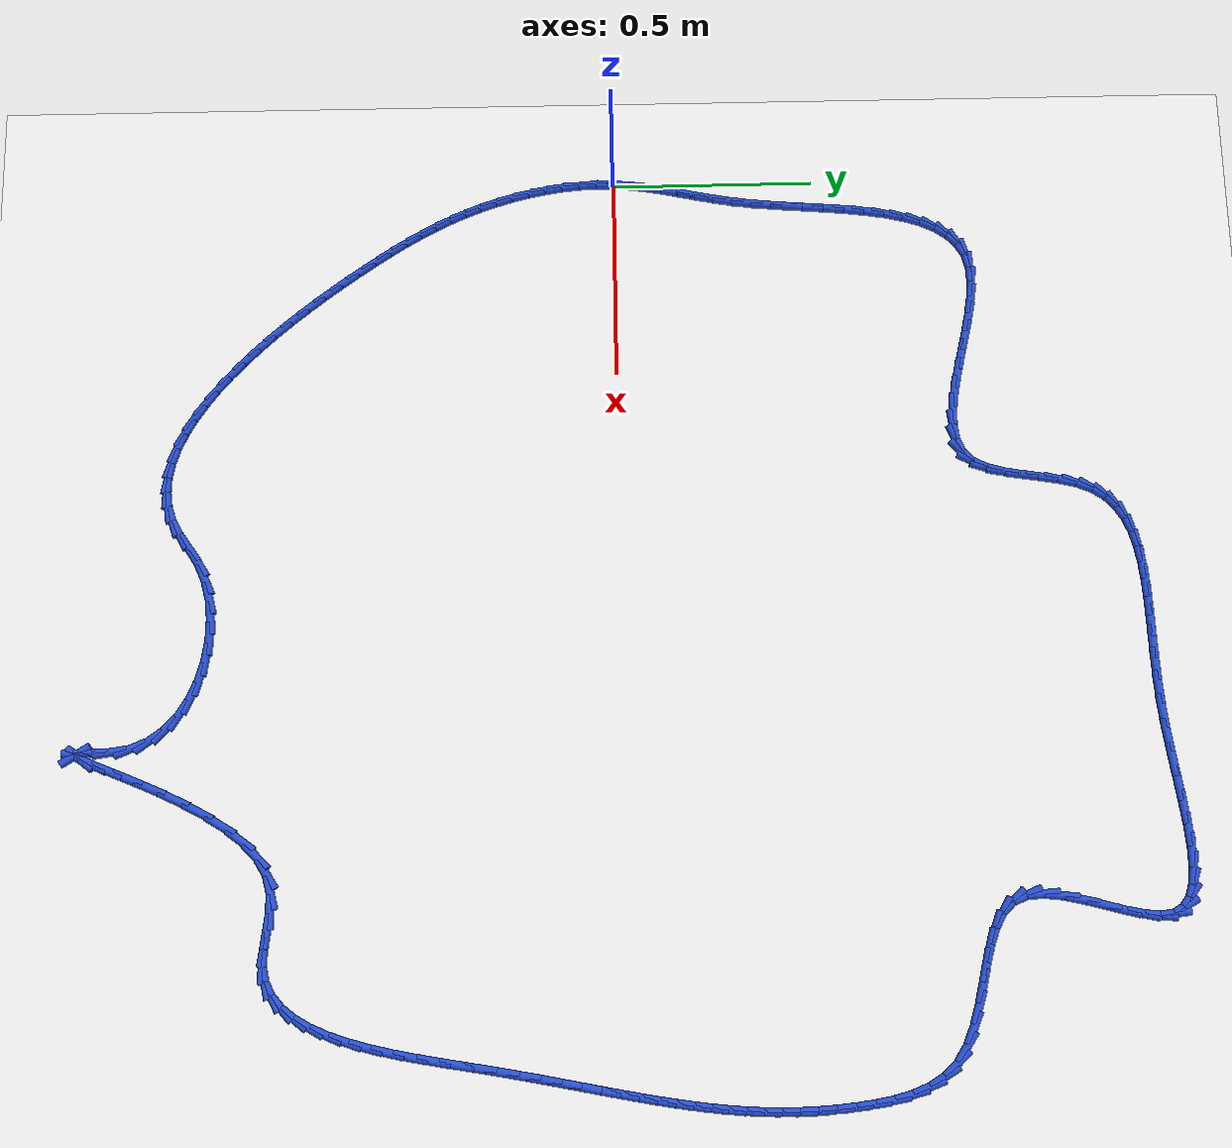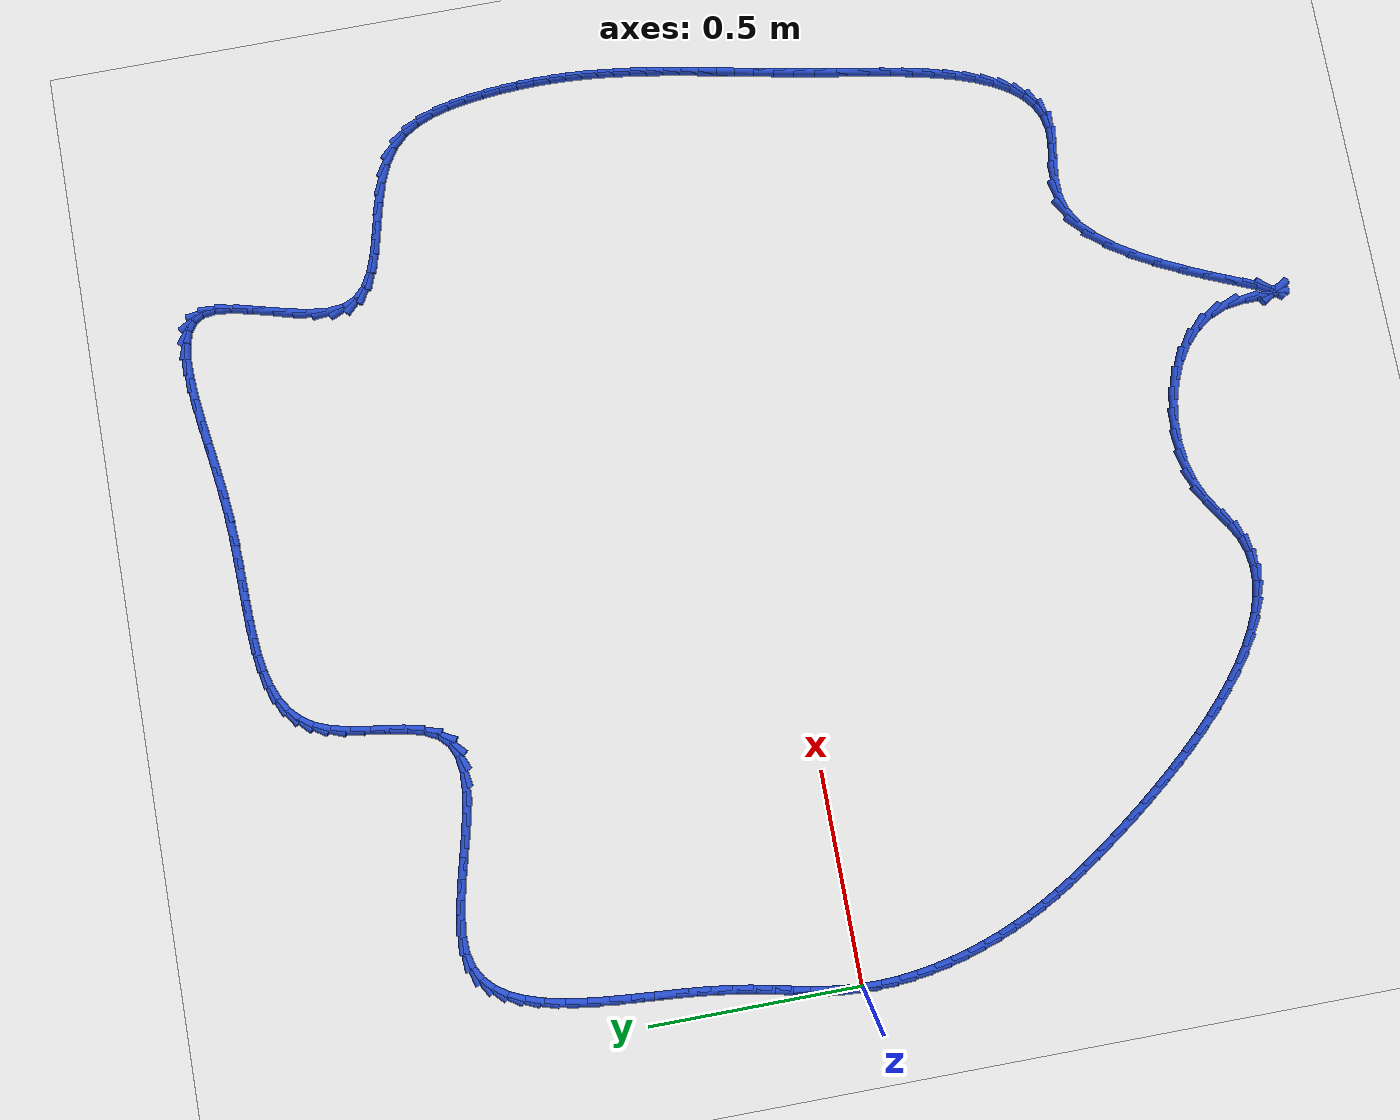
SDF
<sdf version="1.6">
 <world name="default">
  <light name="sun" type="directional">
   <pose>0 0 10 0 -0 0</pose>
   <diffuse>0.8 0.8 0.8 1</diffuse>
   <specular>0.2 0.2 0.2 1</specular>
   <attenuation>
    <range>1000</range>
    <constant>0.9</constant>
    <linear>0.01</linear>
    <quadratic>0.001</quadratic>
   </attenuation>
   <direction>-0.5 0.1 -0.9</direction>
  </light>
  <model name="ground_plane">
   <static>1</static>
   <link name="link">
    <collision name="collision">
     <geometry><plane><normal>0 0 1</normal><size>100 100</size></plane></geometry>
     <surface><friction><ode><mu>100</mu><mu2>50</mu2></ode></friction></surface>
    </collision>
    <visual name="visual">
     <cast_shadows>0</cast_shadows>
     <geometry><plane><normal>0 0 1</normal><size>100 100</size></plane></geometry>
     <material>
      <script><uri>file://media/materials/scripts/gazebo.material</uri><name>Gazebo/WhiteGlow</name></script>
     </material>
    </visual>
   </link>
  </model>
  <gravity>0 0 -9.8</gravity>
  <magnetic_field>6e-06 2.3e-05 -4.2e-05</magnetic_field>
  <atmosphere type="adiabatic"/>
  <physics name="default_physics" default="0" type="ode">
   <max_step_size>0.001</max_step_size>
   <real_time_factor>1</real_time_factor>
   <real_time_update_rate>1000</real_time_update_rate>
  </physics>
  <scene><ambient>0.4 0.4 0.4 1</ambient><background>0.7 0.7 0.7 1</background><shadows>1</shadows></scene>
  <spherical_coordinates>
   <surface_model>EARTH_WGS84</surface_model>
   <latitude_deg>0</latitude_deg>
   <longitude_deg>0</longitude_deg>
   <elevation>0</elevation>
   <heading_deg>0</heading_deg>
  </spherical_coordinates>
  <model name="line">
   <link name="link_0">
    <pose>-1.734723475976807e-18 1.5959455978986625e-16 0.01 0 1.57 1.4917144993074014</pose>
    <collision name="collision">
     <geometry><cylinder><radius>0.01</radius><length>0.08</length></cylinder></geometry>
    </collision>
    <visual name="visual">
     <material>
      <script><name>Gazebo/Blue</name><uri>file://media/materials/scripts/gazebo.material</uri></script>
     </material>
     <geometry><cylinder><radius>0.01</radius><length>0.08</length></cylinder></geometry>
    </visual>
   </link>
   <link name="link_1">
    <pose>0.0032122889012655086 0.040535097974109334 0.01 0 1.57 1.436795211936674</pose>
    <collision name="collision">
     <geometry><cylinder><radius>0.01</radius><length>0.08</length></cylinder></geometry>
    </collision>
    <visual name="visual">
     <material>
      <script><name>Gazebo/Blue</name><uri>file://media/materials/scripts/gazebo.material</uri></script>
     </material>
     <geometry><cylinder><radius>0.01</radius><length>0.08</length></cylinder></geometry>
    </visual>
   </link>
   <link name="link_2">
    <pose>0.008602145523316692 0.08051653631881804 0.01 0 1.57 1.3968337575893583</pose>
    <collision name="collision">
     <geometry><cylinder><radius>0.01</radius><length>0.08</length></cylinder></geometry>
    </collision>
    <visual name="visual">
     <material>
      <script><name>Gazebo/Blue</name><uri>file://media/materials/scripts/gazebo.material</uri></script>
     </material>
     <geometry><cylinder><radius>0.01</radius><length>0.08</length></cylinder></geometry>
    </visual>
   </link>
   <link name="link_3">
    <pose>0.015613409360291696 0.12041243764119046 0.01 0 1.57 1.3729039591032515</pose>
    <collision name="collision">
     <geometry><cylinder><radius>0.01</radius><length>0.08</length></cylinder></geometry>
    </collision>
    <visual name="visual">
     <material>
      <script><name>Gazebo/Blue</name><uri>file://media/materials/scripts/gazebo.material</uri></script>
     </material>
     <geometry><cylinder><radius>0.01</radius><length>0.08</length></cylinder></geometry>
    </visual>
   </link>
   <link name="link_4">
    <pose>0.023689919906328627 0.16069092454829073 0.01 0 1.57 1.365004495759124</pose>
    <collision name="collision">
     <geometry><cylinder><radius>0.01</radius><length>0.08</length></cylinder></geometry>
    </collision>
    <visual name="visual">
     <material>
      <script><name>Gazebo/Blue</name><uri>file://media/materials/scripts/gazebo.material</uri></script>
     </material>
     <geometry><cylinder><radius>0.01</radius><length>0.08</length></cylinder></geometry>
    </visual>
   </link>
   <link name="link_5">
    <pose>0.032275516655565675 0.20182011964718308 0.01 0 1.57 1.372292932320048</pose>
    <collision name="collision">
     <geometry><cylinder><radius>0.01</radius><length>0.08</length></cylinder></geometry>
    </collision>
    <visual name="visual">
     <material>
      <script><name>Gazebo/Blue</name><uri>file://media/materials/scripts/gazebo.material</uri></script>
     </material>
     <geometry><cylinder><radius>0.01</radius><length>0.08</length></cylinder></geometry>
    </visual>
   </link>
   <link name="link_6">
    <pose>0.04081403910214094 0.24426814554493162 0.01 0 1.57 1.3932948616958882</pose>
    <collision name="collision">
     <geometry><cylinder><radius>0.01</radius><length>0.08</length></cylinder></geometry>
    </collision>
    <visual name="visual">
     <material>
      <script><name>Gazebo/Blue</name><uri>file://media/materials/scripts/gazebo.material</uri></script>
     </material>
     <geometry><cylinder><radius>0.01</radius><length>0.08</length></cylinder></geometry>
    </visual>
   </link>
   <link name="link_7">
    <pose>0.04874932674019256 0.2885031248486005 0.01 0 1.57 1.4260205735504552</pose>
    <collision name="collision">
     <geometry><cylinder><radius>0.01</radius><length>0.08</length></cylinder></geometry>
    </collision>
    <visual name="visual">
     <material>
      <script><name>Gazebo/Blue</name><uri>file://media/materials/scripts/gazebo.material</uri></script>
     </material>
     <geometry><cylinder><radius>0.01</radius><length>0.08</length></cylinder></geometry>
    </visual>
   </link>
   <link name="link_8">
    <pose>0.055527071072225063 0.33499104839182847 0.01 0 1.57 1.4609592371503337</pose>
    <collision name="collision">
     <geometry><cylinder><radius>0.01</radius><length>0.08</length></cylinder></geometry>
    </collision>
    <visual name="visual">
     <material>
      <script><name>Gazebo/Blue</name><uri>file://media/materials/scripts/gazebo.material</uri></script>
     </material>
     <geometry><cylinder><radius>0.01</radius><length>0.08</length></cylinder></geometry>
    </visual>
   </link>
   <link name="link_9">
    <pose>0.06091302109982317 0.38382950150664735 0.01 0 1.57 1.483079889269254</pose>
    <collision name="collision">
     <geometry><cylinder><radius>0.01</radius><length>0.08</length></cylinder></geometry>
    </collision>
    <visual name="visual">
     <material>
      <script><name>Gazebo/Blue</name><uri>file://media/materials/scripts/gazebo.material</uri></script>
     </material>
     <geometry><cylinder><radius>0.01</radius><length>0.08</length></cylinder></geometry>
    </visual>
   </link>
   <link name="link_10">
    <pose>0.06535429671786512 0.4343317704961793 0.01 0 1.57 1.4924993723851525</pose>
    <collision name="collision">
     <geometry><cylinder><radius>0.01</radius><length>0.08</length></cylinder></geometry>
    </collision>
    <visual name="visual">
     <material>
      <script><name>Gazebo/Blue</name><uri>file://media/materials/scripts/gazebo.material</uri></script>
     </material>
     <geometry><cylinder><radius>0.01</radius><length>0.08</length></cylinder></geometry>
    </visual>
   </link>
   <link name="link_11">
    <pose>0.06938534506794061 0.4857106227311014 0.01 0 1.57 1.4902363887045131</pose>
    <collision name="collision">
     <geometry><cylinder><radius>0.01</radius><length>0.08</length></cylinder></geometry>
    </collision>
    <visual name="visual">
     <material>
      <script><name>Gazebo/Blue</name><uri>file://media/materials/scripts/gazebo.material</uri></script>
     </material>
     <geometry><cylinder><radius>0.01</radius><length>0.08</length></cylinder></geometry>
    </visual>
   </link>
   <link name="link_12">
    <pose>0.07354061329163925 0.5371788255820903 0.01 0 1.57 1.4762610544672632</pose>
    <collision name="collision">
     <geometry><cylinder><radius>0.01</radius><length>0.08</length></cylinder></geometry>
    </collision>
    <visual name="visual">
     <material>
      <script><name>Gazebo/Blue</name><uri>file://media/materials/scripts/gazebo.material</uri></script>
     </material>
     <geometry><cylinder><radius>0.01</radius><length>0.08</length></cylinder></geometry>
    </visual>
   </link>
   <link name="link_13">
    <pose>0.07835454853055078 0.5879491464198231 0.01 0 1.57 1.4495111345499847</pose>
    <collision name="collision">
     <geometry><cylinder><radius>0.01</radius><length>0.08</length></cylinder></geometry>
    </collision>
    <visual name="visual">
     <material>
      <script><name>Gazebo/Blue</name><uri>file://media/materials/scripts/gazebo.material</uri></script>
     </material>
     <geometry><cylinder><radius>0.01</radius><length>0.08</length></cylinder></geometry>
    </visual>
   </link>
   <link name="link_14">
    <pose>0.08436159792626478 0.6372343526149764 0.01 0 1.57 1.4077358802722113</pose>
    <collision name="collision">
     <geometry><cylinder><radius>0.01</radius><length>0.08</length></cylinder></geometry>
    </collision>
    <visual name="visual">
     <material>
      <script><name>Gazebo/Blue</name><uri>file://media/materials/scripts/gazebo.material</uri></script>
     </material>
     <geometry><cylinder><radius>0.01</radius><length>0.08</length></cylinder></geometry>
    </visual>
   </link>
   <link name="link_15">
    <pose>0.09209620862037099 0.6842472115382272 0.01 0 1.57 1.347163154516065</pose>
    <collision name="collision">
     <geometry><cylinder><radius>0.01</radius><length>0.08</length></cylinder></geometry>
    </collision>
    <visual name="visual">
     <material>
      <script><name>Gazebo/Blue</name><uri>file://media/materials/scripts/gazebo.material</uri></script>
     </material>
     <geometry><cylinder><radius>0.01</radius><length>0.08</length></cylinder></geometry>
    </visual>
   </link>
   <link name="link_16">
    <pose>0.10209282775445905 0.7282004905602527 0.01 0 1.57 1.2620208555017312</pose>
    <collision name="collision">
     <geometry><cylinder><radius>0.01</radius><length>0.08</length></cylinder></geometry>
    </collision>
    <visual name="visual">
     <material>
      <script><name>Gazebo/Blue</name><uri>file://media/materials/scripts/gazebo.material</uri></script>
     </material>
     <geometry><cylinder><radius>0.01</radius><length>0.08</length></cylinder></geometry>
    </visual>
   </link>
   <link name="link_17">
    <pose>0.11488590247011861 0.7683069570517295 0.01 0 1.57 1.1441653393790003</pose>
    <collision name="collision">
     <geometry><cylinder><radius>0.01</radius><length>0.08</length></cylinder></geometry>
    </collision>
    <visual name="visual">
     <material>
      <script><name>Gazebo/Blue</name><uri>file://media/materials/scripts/gazebo.material</uri></script>
     </material>
     <geometry><cylinder><radius>0.01</radius><length>0.08</length></cylinder></geometry>
    </visual>
   </link>
   <link name="link_18">
    <pose>0.13100987990893936 0.8037793783833346 0.01 0 1.57 0.9838257909820284</pose>
    <collision name="collision">
     <geometry><cylinder><radius>0.01</radius><length>0.08</length></cylinder></geometry>
    </collision>
    <visual name="visual">
     <material>
      <script><name>Gazebo/Blue</name><uri>file://media/materials/scripts/gazebo.material</uri></script>
     </material>
     <geometry><cylinder><radius>0.01</radius><length>0.08</length></cylinder></geometry>
    </visual>
   </link>
   <link name="link_19">
    <pose>0.1509992072125109 0.8338305219257445 0.01 0 1.57 0.7740681221431515</pose>
    <collision name="collision">
     <geometry><cylinder><radius>0.01</radius><length>0.08</length></cylinder></geometry>
    </collision>
    <visual name="visual">
     <material>
      <script><name>Gazebo/Blue</name><uri>file://media/materials/scripts/gazebo.material</uri></script>
     </material>
     <geometry><cylinder><radius>0.01</radius><length>0.08</length></cylinder></geometry>
    </visual>
   </link>
   <link name="link_20">
    <pose>0.17538833152242303 0.8576731550496365 0.01 0 1.57 0.5214742011759924</pose>
    <collision name="collision">
     <geometry><cylinder><radius>0.01</radius><length>0.08</length></cylinder></geometry>
    </collision>
    <visual name="visual">
     <material>
      <script><name>Gazebo/Blue</name><uri>file://media/materials/scripts/gazebo.material</uri></script>
     </material>
     <geometry><cylinder><radius>0.01</radius><length>0.08</length></cylinder></geometry>
    </visual>
   </link>
   <link name="link_21">
    <pose>0.2047116999802653 0.8745200451256875 0.01 0 1.57 0.2564635529898381</pose>
    <collision name="collision">
     <geometry><cylinder><radius>0.01</radius><length>0.08</length></cylinder></geometry>
    </collision>
    <visual name="visual">
     <material>
      <script><name>Gazebo/Blue</name><uri>file://media/materials/scripts/gazebo.material</uri></script>
     </material>
     <geometry><cylinder><radius>0.01</radius><length>0.08</length></cylinder></geometry>
    </visual>
   </link>
   <link name="link_22">
    <pose>0.23946821857374254 0.8836345380011811 0.01 0 1.57 0.04445835535896166</pose>
    <collision name="collision">
     <geometry><cylinder><radius>0.01</radius><length>0.08</length></cylinder></geometry>
    </collision>
    <visual name="visual">
     <material>
      <script><name>Gazebo/Blue</name><uri>file://media/materials/scripts/gazebo.material</uri></script>
     </material>
     <geometry><cylinder><radius>0.01</radius><length>0.08</length></cylinder></geometry>
    </visual>
   </link>
   <link name="link_23">
    <pose>0.2793631770077128 0.885409371740848 0.01 0 1.57 -0.0921269365347066</pose>
    <collision name="collision">
     <geometry><cylinder><radius>0.01</radius><length>0.08</length></cylinder></geometry>
    </collision>
    <visual name="visual">
     <material>
      <script><name>Gazebo/Blue</name><uri>file://media/materials/scripts/gazebo.material</uri></script>
     </material>
     <geometry><cylinder><radius>0.01</radius><length>0.08</length></cylinder></geometry>
    </visual>
   </link>
   <link name="link_24">
    <pose>0.32332126622617946 0.8813481514424115 0.01 0 1.57 -0.17607831083229047</pose>
    <collision name="collision">
     <geometry><cylinder><radius>0.01</radius><length>0.08</length></cylinder></geometry>
    </collision>
    <visual name="visual">
     <material>
      <script><name>Gazebo/Blue</name><uri>file://media/materials/scripts/gazebo.material</uri></script>
     </material>
     <geometry><cylinder><radius>0.01</radius><length>0.08</length></cylinder></geometry>
    </visual>
   </link>
   <link name="link_25">
    <pose>0.370234239746904 0.8730013553256086 0.01 0 1.57 -0.22347979675174884</pose>
    <collision name="collision">
     <geometry><cylinder><radius>0.01</radius><length>0.08</length></cylinder></geometry>
    </collision>
    <visual name="visual">
     <material>
      <script><name>Gazebo/Blue</name><uri>file://media/materials/scripts/gazebo.material</uri></script>
     </material>
     <geometry><cylinder><radius>0.01</radius><length>0.08</length></cylinder></geometry>
    </visual>
   </link>
   <link name="link_26">
    <pose>0.4189938510876488 0.8619194616101782 0.01 0 1.57 -0.24292428889392356</pose>
    <collision name="collision">
     <geometry><cylinder><radius>0.01</radius><length>0.08</length></cylinder></geometry>
    </collision>
    <visual name="visual">
     <material>
      <script><name>Gazebo/Blue</name><uri>file://media/materials/scripts/gazebo.material</uri></script>
     </material>
     <geometry><cylinder><radius>0.01</radius><length>0.08</length></cylinder></geometry>
    </visual>
   </link>
   <link name="link_27">
    <pose>0.46849185376617486 0.8496529485158576 0.01 0 1.57 -0.2376590550075612</pose>
    <collision name="collision">
     <geometry><cylinder><radius>0.01</radius><length>0.08</length></cylinder></geometry>
    </collision>
    <visual name="visual">
     <material>
      <script><name>Gazebo/Blue</name><uri>file://media/materials/scripts/gazebo.material</uri></script>
     </material>
     <geometry><cylinder><radius>0.01</radius><length>0.08</length></cylinder></geometry>
    </visual>
   </link>
   <link name="link_28">
    <pose>0.5176200013002447 0.8377522942623854 0.01 0 1.57 -0.20654608577921593</pose>
    <collision name="collision">
     <geometry><cylinder><radius>0.01</radius><length>0.08</length></cylinder></geometry>
    </collision>
    <visual name="visual">
     <material>
      <script><name>Gazebo/Blue</name><uri>file://media/materials/scripts/gazebo.material</uri></script>
     </material>
     <geometry><cylinder><radius>0.01</radius><length>0.08</length></cylinder></geometry>
    </visual>
   </link>
   <link name="link_29">
    <pose>0.5652700472076201 0.8277679770694997 0.01 0 1.57 -0.14363270235722891</pose>
    <collision name="collision">
     <geometry><cylinder><radius>0.01</radius><length>0.08</length></cylinder></geometry>
    </collision>
    <visual name="visual">
     <material>
      <script><name>Gazebo/Blue</name><uri>file://media/materials/scripts/gazebo.material</uri></script>
     </material>
     <geometry><cylinder><radius>0.01</radius><length>0.08</length></cylinder></geometry>
    </visual>
   </link>
   <link name="link_30">
    <pose>0.6103337450060623 0.8212504751569379 0.01 0 1.57 -0.03624809785809501</pose>
    <collision name="collision">
     <geometry><cylinder><radius>0.01</radius><length>0.08</length></cylinder></geometry>
    </collision>
    <visual name="visual">
     <material>
      <script><name>Gazebo/Blue</name><uri>file://media/materials/scripts/gazebo.material</uri></script>
     </material>
     <geometry><cylinder><radius>0.01</radius><length>0.08</length></cylinder></geometry>
    </visual>
   </link>
   <link name="link_31">
    <pose>0.6517028482133338 0.8197502667444387 0.01 0 1.57 0.1377086213476879</pose>
    <collision name="collision">
     <geometry><cylinder><radius>0.01</radius><length>0.08</length></cylinder></geometry>
    </collision>
    <visual name="visual">
     <material>
      <script><name>Gazebo/Blue</name><uri>file://media/materials/scripts/gazebo.material</uri></script>
     </material>
     <geometry><cylinder><radius>0.01</radius><length>0.08</length></cylinder></geometry>
    </visual>
   </link>
   <link name="link_32">
    <pose>0.6882691103471957 0.8248178300517399 0.01 0 1.57 0.4062106025662297</pose>
    <collision name="collision">
     <geometry><cylinder><radius>0.01</radius><length>0.08</length></cylinder></geometry>
    </collision>
    <visual name="visual">
     <material>
      <script><name>Gazebo/Blue</name><uri>file://media/materials/scripts/gazebo.material</uri></script>
     </material>
     <geometry><cylinder><radius>0.01</radius><length>0.08</length></cylinder></geometry>
    </visual>
   </link>
   <link name="link_33">
    <pose>0.7189242849254107 0.8380036432985797 0.01 0 1.57 0.7677330033355623</pose>
    <collision name="collision">
     <geometry><cylinder><radius>0.01</radius><length>0.08</length></cylinder></geometry>
    </collision>
    <visual name="visual">
     <material>
      <script><name>Gazebo/Blue</name><uri>file://media/materials/scripts/gazebo.material</uri></script>
     </material>
     <geometry><cylinder><radius>0.01</radius><length>0.08</length></cylinder></geometry>
    </visual>
   </link>
   <link name="link_34">
    <pose>0.7425769982312006 0.8608351205123197 0.01 0 1.57 1.0967866905146695</pose>
    <collision name="collision">
     <geometry><cylinder><radius>0.01</radius><length>0.08</length></cylinder></geometry>
    </collision>
    <visual name="visual">
     <material>
      <script><name>Gazebo/Blue</name><uri>file://media/materials/scripts/gazebo.material</uri></script>
     </material>
     <geometry><cylinder><radius>0.01</radius><length>0.08</length></cylinder></geometry>
    </visual>
   </link>
   <link name="link_35">
    <pose>0.7592445493013653 0.8933241777582319 0.01 0 1.57 1.289605686738009</pose>
    <collision name="collision">
     <geometry><cylinder><radius>0.01</radius><length>0.08</length></cylinder></geometry>
    </collision>
    <visual name="visual">
     <material>
      <script><name>Gazebo/Blue</name><uri>file://media/materials/scripts/gazebo.material</uri></script>
     </material>
     <geometry><cylinder><radius>0.01</radius><length>0.08</length></cylinder></geometry>
    </visual>
   </link>
   <link name="link_36">
    <pose>0.7707204703533036 0.9330547127736274 0.01 0 1.57 1.3870984843166103</pose>
    <collision name="collision">
     <geometry><cylinder><radius>0.01</radius><length>0.08</length></cylinder></geometry>
    </collision>
    <visual name="visual">
     <material>
      <script><name>Gazebo/Blue</name><uri>file://media/materials/scripts/gazebo.material</uri></script>
     </material>
     <geometry><cylinder><radius>0.01</radius><length>0.08</length></cylinder></geometry>
    </visual>
   </link>
   <link name="link_37">
    <pose>0.778958047722516 0.9773922477295035 0.01 0 1.57 1.421779429042974</pose>
    <collision name="collision">
     <geometry><cylinder><radius>0.01</radius><length>0.08</length></cylinder></geometry>
    </collision>
    <visual name="visual">
     <material>
      <script><name>Gazebo/Blue</name><uri>file://media/materials/scripts/gazebo.material</uri></script>
     </material>
     <geometry><cylinder><radius>0.01</radius><length>0.08</length></cylinder></geometry>
    </visual>
   </link>
   <link name="link_38">
    <pose>0.7859105677445027 1.0237023047968568 0.01 0 1.57 1.4053762811008794</pose>
    <collision name="collision">
     <geometry><cylinder><radius>0.01</radius><length>0.08</length></cylinder></geometry>
    </collision>
    <visual name="visual">
     <material>
      <script><name>Gazebo/Blue</name><uri>file://media/materials/scripts/gazebo.material</uri></script>
     </material>
     <geometry><cylinder><radius>0.01</radius><length>0.08</length></cylinder></geometry>
    </visual>
   </link>
   <link name="link_39">
    <pose>0.7935313167547653 1.0693504061466859 0.01 0 1.57 1.333513691290035</pose>
    <collision name="collision">
     <geometry><cylinder><radius>0.01</radius><length>0.08</length></cylinder></geometry>
    </collision>
    <visual name="visual">
     <material>
      <script><name>Gazebo/Blue</name><uri>file://media/materials/scripts/gazebo.material</uri></script>
     </material>
     <geometry><cylinder><radius>0.01</radius><length>0.08</length></cylinder></geometry>
    </visual>
   </link>
   <link name="link_40">
    <pose>0.8037735810888035 1.1117020739499865 0.01 0 1.57 1.1870362396480312</pose>
    <collision name="collision">
     <geometry><cylinder><radius>0.01</radius><length>0.08</length></cylinder></geometry>
    </collision>
    <visual name="visual">
     <material>
      <script><name>Gazebo/Blue</name><uri>file://media/materials/scripts/gazebo.material</uri></script>
     </material>
     <geometry><cylinder><radius>0.01</radius><length>0.08</length></cylinder></geometry>
    </visual>
   </link>
   <link name="link_41">
    <pose>0.8185207587202704 1.148224946677394 0.01 0 1.57 0.9824375289127192</pose>
    <collision name="collision">
     <geometry><cylinder><radius>0.01</radius><length>0.08</length></cylinder></geometry>
    </collision>
    <visual name="visual">
     <material>
      <script><name>Gazebo/Blue</name><uri>file://media/materials/scripts/gazebo.material</uri></script>
     </material>
     <geometry><cylinder><radius>0.01</radius><length>0.08</length></cylinder></geometry>
    </visual>
   </link>
   <link name="link_42">
    <pose>0.8384680415801128 1.1781227916925188 0.01 0 1.57 0.7665219037315856</pose>
    <collision name="collision">
     <geometry><cylinder><radius>0.01</radius><length>0.08</length></cylinder></geometry>
    </collision>
    <visual name="visual">
     <material>
      <script><name>Gazebo/Blue</name><uri>file://media/materials/scripts/gazebo.material</uri></script>
     </material>
     <geometry><cylinder><radius>0.01</radius><length>0.08</length></cylinder></geometry>
    </visual>
   </link>
   <link name="link_43">
    <pose>0.8633171152033959 1.2020510228725036 0.01 0 1.57 0.5651695614560587</pose>
    <collision name="collision">
     <geometry><cylinder><radius>0.01</radius><length>0.08</length></cylinder></geometry>
    </collision>
    <visual name="visual">
     <material>
      <script><name>Gazebo/Blue</name><uri>file://media/materials/scripts/gazebo.material</uri></script>
     </material>
     <geometry><cylinder><radius>0.01</radius><length>0.08</length></cylinder></geometry>
    </visual>
   </link>
   <link name="link_44">
    <pose>0.8927391080504764 1.2207097020918718 0.01 0 1.57 0.3963509982696934</pose>
    <collision name="collision">
     <geometry><cylinder><radius>0.01</radius><length>0.08</length></cylinder></geometry>
    </collision>
    <visual name="visual">
     <material>
      <script><name>Gazebo/Blue</name><uri>file://media/materials/scripts/gazebo.material</uri></script>
     </material>
     <geometry><cylinder><radius>0.01</radius><length>0.08</length></cylinder></geometry>
    </visual>
   </link>
   <link name="link_45">
    <pose>0.9264051485817119 1.2347988912251484 0.01 0 1.57 0.26551727182705664</pose>
    <collision name="collision">
     <geometry><cylinder><radius>0.01</radius><length>0.08</length></cylinder></geometry>
    </collision>
    <visual name="visual">
     <material>
      <script><name>Gazebo/Blue</name><uri>file://media/materials/scripts/gazebo.material</uri></script>
     </material>
     <geometry><cylinder><radius>0.01</radius><length>0.08</length></cylinder></geometry>
    </visual>
   </link>
   <link name="link_46">
    <pose>0.963986365257459 1.2450186521468571 0.01 0 1.57 0.16961556980617587</pose>
    <collision name="collision">
     <geometry><cylinder><radius>0.01</radius><length>0.08</length></cylinder></geometry>
    </collision>
    <visual name="visual">
     <material>
      <script><name>Gazebo/Blue</name><uri>file://media/materials/scripts/gazebo.material</uri></script>
     </material>
     <geometry><cylinder><radius>0.01</radius><length>0.08</length></cylinder></geometry>
    </visual>
   </link>
   <link name="link_47">
    <pose>1.0051538865380751 1.2520690467315219 0.01 0 1.57 0.1027565488308258</pose>
    <collision name="collision">
     <geometry><cylinder><radius>0.01</radius><length>0.08</length></cylinder></geometry>
    </collision>
    <visual name="visual">
     <material>
      <script><name>Gazebo/Blue</name><uri>file://media/materials/scripts/gazebo.material</uri></script>
     </material>
     <geometry><cylinder><radius>0.01</radius><length>0.08</length></cylinder></geometry>
    </visual>
   </link>
   <link name="link_48">
    <pose>1.0495788408839177 1.2566501368536676 0.01 0 1.57 0.05931026710495304</pose>
    <collision name="collision">
     <geometry><cylinder><radius>0.01</radius><length>0.08</length></cylinder></geometry>
    </collision>
    <visual name="visual">
     <material>
      <script><name>Gazebo/Blue</name><uri>file://media/materials/scripts/gazebo.material</uri></script>
     </material>
     <geometry><cylinder><radius>0.01</radius><length>0.08</length></cylinder></geometry>
    </visual>
   </link>
   <link name="link_49">
    <pose>1.0969323567553437 1.259461984387818 0.01 0 1.57 0.03487184348121867</pose>
    <collision name="collision">
     <geometry><cylinder><radius>0.01</radius><length>0.08</length></cylinder></geometry>
    </collision>
    <visual name="visual">
     <material>
      <script><name>Gazebo/Blue</name><uri>file://media/materials/scripts/gazebo.material</uri></script>
     </material>
     <geometry><cylinder><radius>0.01</radius><length>0.08</length></cylinder></geometry>
    </visual>
   </link>
   <link name="link_50">
    <pose>1.1468855626127104 1.2612046512084976 0.01 0 1.57 0.02629501298949246</pose>
    <collision name="collision">
     <geometry><cylinder><radius>0.01</radius><length>0.08</length></cylinder></geometry>
    </collision>
    <visual name="visual">
     <material>
      <script><name>Gazebo/Blue</name><uri>file://media/materials/scripts/gazebo.material</uri></script>
     </material>
     <geometry><cylinder><radius>0.01</radius><length>0.08</length></cylinder></geometry>
    </visual>
   </link>
   <link name="link_51">
    <pose>1.1991095869163748 1.2625781991902303 0.01 0 1.57 0.03145754982673294</pose>
    <collision name="collision">
     <geometry><cylinder><radius>0.01</radius><length>0.08</length></cylinder></geometry>
    </collision>
    <visual name="visual">
     <material>
      <script><name>Gazebo/Blue</name><uri>file://media/materials/scripts/gazebo.material</uri></script>
     </material>
     <geometry><cylinder><radius>0.01</radius><length>0.08</length></cylinder></geometry>
    </visual>
   </link>
   <link name="link_52">
    <pose>1.2532755581266946 1.264282690207541 0.01 0 1.57 0.04900238034284818</pose>
    <collision name="collision">
     <geometry><cylinder><radius>0.01</radius><length>0.08</length></cylinder></geometry>
    </collision>
    <visual name="visual">
     <material>
      <script><name>Gazebo/Blue</name><uri>file://media/materials/scripts/gazebo.material</uri></script>
     </material>
     <geometry><cylinder><radius>0.01</radius><length>0.08</length></cylinder></geometry>
    </visual>
   </link>
   <link name="link_53">
    <pose>1.3090546047040261 1.2670181861349539 0.01 0 1.57 0.07811366855033214</pose>
    <collision name="collision">
     <geometry><cylinder><radius>0.01</radius><length>0.08</length></cylinder></geometry>
    </collision>
    <visual name="visual">
     <material>
      <script><name>Gazebo/Blue</name><uri>file://media/materials/scripts/gazebo.material</uri></script>
     </material>
     <geometry><cylinder><radius>0.01</radius><length>0.08</length></cylinder></geometry>
    </visual>
   </link>
   <link name="link_54">
    <pose>1.3661178331877208 1.271484692443205 0.01 0 1.57 0.11296170687729365</pose>
    <collision name="collision">
     <geometry><cylinder><radius>0.01</radius><length>0.08</length></cylinder></geometry>
    </collision>
    <visual name="visual">
     <material>
      <script><name>Gazebo/Blue</name><uri>file://media/materials/scripts/gazebo.material</uri></script>
     </material>
     <geometry><cylinder><radius>0.01</radius><length>0.08</length></cylinder></geometry>
    </visual>
   </link>
   <link name="link_55">
    <pose>1.4240080237495347 1.2780520247861151 0.01 0 1.57 0.1362757803306267</pose>
    <collision name="collision">
     <geometry><cylinder><radius>0.01</radius><length>0.08</length></cylinder></geometry>
    </collision>
    <visual name="visual">
     <material>
      <script><name>Gazebo/Blue</name><uri>file://media/materials/scripts/gazebo.material</uri></script>
     </material>
     <geometry><cylinder><radius>0.01</radius><length>0.08</length></cylinder></geometry>
    </visual>
   </link>
   <link name="link_56">
    <pose>1.4818373021110742 1.2859819045363818 0.01 0 1.57 0.1455029048446189</pose>
    <collision name="collision">
     <geometry><cylinder><radius>0.01</radius><length>0.08</length></cylinder></geometry>
    </collision>
    <visual name="visual">
     <material>
      <script><name>Gazebo/Blue</name><uri>file://media/materials/scripts/gazebo.material</uri></script>
     </material>
     <geometry><cylinder><radius>0.01</radius><length>0.08</length></cylinder></geometry>
    </visual>
   </link>
   <link name="link_57">
    <pose>1.538627554511207 1.2943038626069878 0.01 0 1.57 0.14044458529298665</pose>
    <collision name="collision">
     <geometry><cylinder><radius>0.01</radius><length>0.08</length></cylinder></geometry>
    </collision>
    <visual name="visual">
     <material>
      <script><name>Gazebo/Blue</name><uri>file://media/materials/scripts/gazebo.material</uri></script>
     </material>
     <geometry><cylinder><radius>0.01</radius><length>0.08</length></cylinder></geometry>
    </visual>
   </link>
   <link name="link_58">
    <pose>1.5934006671887977 1.3020474299109164 0.01 0 1.57 0.11907410465653506</pose>
    <collision name="collision">
     <geometry><cylinder><radius>0.01</radius><length>0.08</length></cylinder></geometry>
    </collision>
    <visual name="visual">
     <material>
      <script><name>Gazebo/Blue</name><uri>file://media/materials/scripts/gazebo.material</uri></script>
     </material>
     <geometry><cylinder><radius>0.01</radius><length>0.08</length></cylinder></geometry>
    </visual>
   </link>
   <link name="link_59">
    <pose>1.6451785263827112 1.3082421373611495 0.01 0 1.57 0.0767325855621983</pose>
    <collision name="collision">
     <geometry><cylinder><radius>0.01</radius><length>0.08</length></cylinder></geometry>
    </collision>
    <visual name="visual">
     <material>
      <script><name>Gazebo/Blue</name><uri>file://media/materials/scripts/gazebo.material</uri></script>
     </material>
     <geometry><cylinder><radius>0.01</radius><length>0.08</length></cylinder></geometry>
    </visual>
   </link>
   <link name="link_60">
    <pose>1.6929830183318149 1.3119175158706708 0.01 0 1.57 0.004330601691064253</pose>
    <collision name="collision">
     <geometry><cylinder><radius>0.01</radius><length>0.08</length></cylinder></geometry>
    </collision>
    <visual name="visual">
     <material>
      <script><name>Gazebo/Blue</name><uri>file://media/materials/scripts/gazebo.material</uri></script>
     </material>
     <geometry><cylinder><radius>0.01</radius><length>0.08</length></cylinder></geometry>
    </visual>
   </link>
   <link name="link_61">
    <pose>1.7358360292749726 1.3121030963524623 0.01 0 1.57 -0.11525858665743724</pose>
    <collision name="collision">
     <geometry><cylinder><radius>0.01</radius><length>0.08</length></cylinder></geometry>
    </collision>
    <visual name="visual">
     <material>
      <script><name>Gazebo/Blue</name><uri>file://media/materials/scripts/gazebo.material</uri></script>
     </material>
     <geometry><cylinder><radius>0.01</radius><length>0.08</length></cylinder></geometry>
    </visual>
   </link>
   <link name="link_62">
    <pose>1.7727594454510516 1.3078284097195072 0.01 0 1.57 -0.31273409508932754</pose>
    <collision name="collision">
     <geometry><cylinder><radius>0.01</radius><length>0.08</length></cylinder></geometry>
    </collision>
    <visual name="visual">
     <material>
      <script><name>Gazebo/Blue</name><uri>file://media/materials/scripts/gazebo.material</uri></script>
     </material>
     <geometry><cylinder><radius>0.01</radius><length>0.08</length></cylinder></geometry>
    </visual>
   </link>
   <link name="link_63">
    <pose>1.8027751530989158 1.2981229868847879 0.01 0 1.57 -0.6291557627518425</pose>
    <collision name="collision">
     <geometry><cylinder><radius>0.01</radius><length>0.08</length></cylinder></geometry>
    </collision>
    <visual name="visual">
     <material>
      <script><name>Gazebo/Blue</name><uri>file://media/materials/scripts/gazebo.material</uri></script>
     </material>
     <geometry><cylinder><radius>0.01</radius><length>0.08</length></cylinder></geometry>
    </visual>
   </link>
   <link name="link_64">
    <pose>1.8249050384574321 1.2820163587612874 0.01 0 1.57 -1.056486914539952</pose>
    <collision name="collision">
     <geometry><cylinder><radius>0.01</radius><length>0.08</length></cylinder></geometry>
    </collision>
    <visual name="visual">
     <material>
      <script><name>Gazebo/Blue</name><uri>file://media/materials/scripts/gazebo.material</uri></script>
     </material>
     <geometry><cylinder><radius>0.01</radius><length>0.08</length></cylinder></geometry>
    </visual>
   </link>
   <link name="link_65">
    <pose>1.838170987765466 1.2585380562619883 0.01 0 1.57 -1.4542742743652997</pose>
    <collision name="collision">
     <geometry><cylinder><radius>0.01</radius><length>0.08</length></cylinder></geometry>
    </collision>
    <visual name="visual">
     <material>
      <script><name>Gazebo/Blue</name><uri>file://media/materials/scripts/gazebo.material</uri></script>
     </material>
     <geometry><cylinder><radius>0.01</radius><length>0.08</length></cylinder></geometry>
    </visual>
   </link>
   <link name="link_66">
    <pose>1.8418692773525025 1.2269428634613 0.01 0 1.57 1.4592407138584311</pose>
    <collision name="collision">
     <geometry><cylinder><radius>0.01</radius><length>0.08</length></cylinder></geometry>
    </collision>
    <visual name="visual">
     <material>
      <script><name>Gazebo/Blue</name><uri>file://media/materials/scripts/gazebo.material</uri></script>
     </material>
     <geometry><cylinder><radius>0.01</radius><length>0.08</length></cylinder></geometry>
    </visual>
   </link>
   <link name="link_67">
    <pose>1.8375439262384095 1.1883307883115641 0.01 0 1.57 1.351908942411549</pose>
    <collision name="collision">
     <geometry><cylinder><radius>0.01</radius><length>0.08</length></cylinder></geometry>
    </collision>
    <visual name="visual">
     <material>
      <script><name>Gazebo/Blue</name><uri>file://media/materials/scripts/gazebo.material</uri></script>
     </material>
     <geometry><cylinder><radius>0.01</radius><length>0.08</length></cylinder></geometry>
    </visual>
   </link>
   <link name="link_68">
    <pose>1.8278393450538029 1.1447051756479083 0.01 0 1.57 1.3102478265604918</pose>
    <collision name="collision">
     <geometry><cylinder><radius>0.01</radius><length>0.08</length></cylinder></geometry>
    </collision>
    <visual name="visual">
     <material>
      <script><name>Gazebo/Blue</name><uri>file://media/materials/scripts/gazebo.material</uri></script>
     </material>
     <geometry><cylinder><radius>0.01</radius><length>0.08</length></cylinder></geometry>
    </visual>
   </link>
   <link name="link_69">
    <pose>1.8154074691554383 1.098075547526904 0.01 0 1.57 1.3139720334394576</pose>
    <collision name="collision">
     <geometry><cylinder><radius>0.01</radius><length>0.08</length></cylinder></geometry>
    </collision>
    <visual name="visual">
     <material>
      <script><name>Gazebo/Blue</name><uri>file://media/materials/scripts/gazebo.material</uri></script>
     </material>
     <geometry><cylinder><radius>0.01</radius><length>0.08</length></cylinder></geometry>
    </visual>
   </link>
   <link name="link_70">
    <pose>1.8029002339000713 1.0504514260051228 0.01 0 1.57 1.3608726053379567</pose>
    <collision name="collision">
     <geometry><cylinder><radius>0.01</radius><length>0.08</length></cylinder></geometry>
    </collision>
    <visual name="visual">
     <material>
      <script><name>Gazebo/Blue</name><uri>file://media/materials/scripts/gazebo.material</uri></script>
     </material>
     <geometry><cylinder><radius>0.01</radius><length>0.08</length></cylinder></geometry>
    </visual>
   </link>
   <link name="link_71">
    <pose>1.7929695746444572 1.003842333139135 0.01 0 1.57 1.4633263212823258</pose>
    <collision name="collision">
     <geometry><cylinder><radius>0.01</radius><length>0.08</length></cylinder></geometry>
    </collision>
    <visual name="visual">
     <material>
      <script><name>Gazebo/Blue</name><uri>file://media/materials/scripts/gazebo.material</uri></script>
     </material>
     <geometry><cylinder><radius>0.01</radius><length>0.08</length></cylinder></geometry>
    </visual>
   </link>
   <link name="link_72">
    <pose>1.7882674267453516 0.9602577909855129 0.01 0 1.57 -1.4885372281886198</pose>
    <collision name="collision">
     <geometry><cylinder><radius>0.01</radius><length>0.08</length></cylinder></geometry>
    </collision>
    <visual name="visual">
     <material>
      <script><name>Gazebo/Blue</name><uri>file://media/materials/scripts/gazebo.material</uri></script>
     </material>
     <geometry><cylinder><radius>0.01</radius><length>0.08</length></cylinder></geometry>
    </visual>
   </link>
   <link name="link_73">
    <pose>1.7914457255595095 0.9217073216008274 0.01 0 1.57 -1.1639242244328496</pose>
    <collision name="collision">
     <geometry><cylinder><radius>0.01</radius><length>0.08</length></cylinder></geometry>
    </collision>
    <visual name="visual">
     <material>
      <script><name>Gazebo/Blue</name><uri>file://media/materials/scripts/gazebo.material</uri></script>
     </material>
     <geometry><cylinder><radius>0.01</radius><length>0.08</length></cylinder></geometry>
    </visual>
   </link>
   <link name="link_74">
    <pose>1.8050556101277941 0.8901238154656408 0.01 0 1.57 -0.7873997077886349</pose>
    <collision name="collision">
     <geometry><cylinder><radius>0.01</radius><length>0.08</length></cylinder></geometry>
    </collision>
    <visual name="visual">
     <material>
      <script><name>Gazebo/Blue</name><uri>file://media/materials/scripts/gazebo.material</uri></script>
     </material>
     <geometry><cylinder><radius>0.01</radius><length>0.08</length></cylinder></geometry>
    </visual>
   </link>
   <link name="link_75">
    <pose>1.8293721411100525 0.8657097478969238 0.01 0 1.57 -0.516217603077784</pose>
    <collision name="collision">
     <geometry><cylinder><radius>0.01</radius><length>0.08</length></cylinder></geometry>
    </collision>
    <visual name="visual">
     <material>
      <script><name>Gazebo/Blue</name><uri>file://media/materials/scripts/gazebo.material</uri></script>
     </material>
     <geometry><cylinder><radius>0.01</radius><length>0.08</length></cylinder></geometry>
    </visual>
   </link>
   <link name="link_76">
    <pose>1.8624175213368517 0.8469548327436205 0.01 0 1.57 -0.35415936212429544</pose>
    <collision name="collision">
     <geometry><cylinder><radius>0.01</radius><length>0.08</length></cylinder></geometry>
    </collision>
    <visual name="visual">
     <material>
      <script><name>Gazebo/Blue</name><uri>file://media/materials/scripts/gazebo.material</uri></script>
     </material>
     <geometry><cylinder><radius>0.01</radius><length>0.08</length></cylinder></geometry>
    </visual>
   </link>
   <link name="link_77">
    <pose>1.9021178015862952 0.8322756831341642 0.01 0 1.57 -0.2685642349403821</pose>
    <collision name="collision">
     <geometry><cylinder><radius>0.01</radius><length>0.08</length></cylinder></geometry>
    </collision>
    <visual name="visual">
     <material>
      <script><name>Gazebo/Blue</name><uri>file://media/materials/scripts/gazebo.material</uri></script>
     </material>
     <geometry><cylinder><radius>0.01</radius><length>0.08</length></cylinder></geometry>
    </visual>
   </link>
   <link name="link_78">
    <pose>1.946399032636487 0.8200889121969883 0.01 0 1.57 -0.2365269665464711</pose>
    <collision name="collision">
     <geometry><cylinder><radius>0.01</radius><length>0.08</length></cylinder></geometry>
    </collision>
    <visual name="visual">
     <material>
      <script><name>Gazebo/Blue</name><uri>file://media/materials/scripts/gazebo.material</uri></script>
     </material>
     <geometry><cylinder><radius>0.01</radius><length>0.08</length></cylinder></geometry>
    </visual>
   </link>
   <link name="link_79">
    <pose>1.9931872652655314 0.8088111330605265 0.01 0 1.57 -0.24790346906114116</pose>
    <collision name="collision">
     <geometry><cylinder><radius>0.01</radius><length>0.08</length></cylinder></geometry>
    </collision>
    <visual name="visual">
     <material>
      <script><name>Gazebo/Blue</name><uri>file://media/materials/scripts/gazebo.material</uri></script>
     </material>
     <geometry><cylinder><radius>0.01</radius><length>0.08</length></cylinder></geometry>
    </visual>
   </link>
   <link name="link_80">
    <pose>2.0404085502515312 0.7968589588532121 0.01 0 1.57 -0.30220685047657836</pose>
    <collision name="collision">
     <geometry><cylinder><radius>0.01</radius><length>0.08</length></cylinder></geometry>
    </collision>
    <visual name="visual">
     <material>
      <script><name>Gazebo/Blue</name><uri>file://media/materials/scripts/gazebo.material</uri></script>
     </material>
     <geometry><cylinder><radius>0.01</radius><length>0.08</length></cylinder></geometry>
    </visual>
   </link>
   <link name="link_81">
    <pose>2.0859889383725916 0.7826490027034786 0.01 0 1.57 -0.40708424234307306</pose>
    <collision name="collision">
     <geometry><cylinder><radius>0.01</radius><length>0.08</length></cylinder></geometry>
    </collision>
    <visual name="visual">
     <material>
      <script><name>Gazebo/Blue</name><uri>file://media/materials/scripts/gazebo.material</uri></script>
     </material>
     <geometry><cylinder><radius>0.01</radius><length>0.08</length></cylinder></geometry>
    </visual>
   </link>
   <link name="link_82">
    <pose>2.1278544804068167 0.7645978777397595 0.01 0 1.57 -0.5768777004514546</pose>
    <collision name="collision">
     <geometry><cylinder><radius>0.01</radius><length>0.08</length></cylinder></geometry>
    </collision>
    <visual name="visual">
     <material>
      <script><name>Gazebo/Blue</name><uri>file://media/materials/scripts/gazebo.material</uri></script>
     </material>
     <geometry><cylinder><radius>0.01</radius><length>0.08</length></cylinder></geometry>
    </visual>
   </link>
   <link name="link_83">
    <pose>2.1639312271323092 0.7411221970904887 0.01 0 1.57 -0.8098221811694225</pose>
    <collision name="collision">
     <geometry><cylinder><radius>0.01</radius><length>0.08</length></cylinder></geometry>
    </collision>
    <visual name="visual">
     <material>
      <script><name>Gazebo/Blue</name><uri>file://media/materials/scripts/gazebo.material</uri></script>
     </material>
     <geometry><cylinder><radius>0.01</radius><length>0.08</length></cylinder></geometry>
    </visual>
   </link>
   <link name="link_84">
    <pose>2.1925728538445797 0.7110461639763306 0.01 0 1.57 -1.0259885748505464</pose>
    <collision name="collision">
     <geometry><cylinder><radius>0.01</radius><length>0.08</length></cylinder></geometry>
    </collision>
    <visual name="visual">
     <material>
      <script><name>Gazebo/Blue</name><uri>file://media/materials/scripts/gazebo.material</uri></script>
     </material>
     <geometry><cylinder><radius>0.01</radius><length>0.08</length></cylinder></geometry>
    </visual>
   </link>
   <link name="link_85">
    <pose>2.2142740364322346 0.6752346752491429 0.01 0 1.57 -1.1923110346708692</pose>
    <collision name="collision">
     <geometry><cylinder><radius>0.01</radius><length>0.08</length></cylinder></geometry>
    </collision>
    <visual name="visual">
     <material>
      <script><name>Gazebo/Blue</name><uri>file://media/materials/scripts/gazebo.material</uri></script>
     </material>
     <geometry><cylinder><radius>0.01</radius><length>0.08</length></cylinder></geometry>
    </visual>
   </link>
   <link name="link_86">
    <pose>2.2301981136859874 0.6351899634673396 0.01 0 1.57 -1.312296114951965</pose>
    <collision name="collision">
     <geometry><cylinder><radius>0.01</radius><length>0.08</length></cylinder></geometry>
    </collision>
    <visual name="visual">
     <material>
      <script><name>Gazebo/Blue</name><uri>file://media/materials/scripts/gazebo.material</uri></script>
     </material>
     <geometry><cylinder><radius>0.01</radius><length>0.08</length></cylinder></geometry>
    </visual>
   </link>
   <link name="link_87">
    <pose>2.2415086483218363 0.5924144746236057 0.01 0 1.57 -1.3940273540027899</pose>
    <collision name="collision">
     <geometry><cylinder><radius>0.01</radius><length>0.08</length></cylinder></geometry>
    </collision>
    <visual name="visual">
     <material>
      <script><name>Gazebo/Blue</name><uri>file://media/materials/scripts/gazebo.material</uri></script>
     </material>
     <geometry><cylinder><radius>0.01</radius><length>0.08</length></cylinder></geometry>
    </visual>
   </link>
   <link name="link_88">
    <pose>2.2493692030557804 0.5484106547106272 0.01 0 1.57 -1.4443224692131036</pose>
    <collision name="collision">
     <geometry><cylinder><radius>0.01</radius><length>0.08</length></cylinder></geometry>
    </collision>
    <visual name="visual">
     <material>
      <script><name>Gazebo/Blue</name><uri>file://media/materials/scripts/gazebo.material</uri></script>
     </material>
     <geometry><cylinder><radius>0.01</radius><length>0.08</length></cylinder></geometry>
    </visual>
   </link>
   <link name="link_89">
    <pose>2.2549318003560996 0.5046632223556308 0.01 0 1.57 -1.478076930266304</pose>
    <collision name="collision">
     <geometry><cylinder><radius>0.01</radius><length>0.08</length></cylinder></geometry>
    </collision>
    <visual name="visual">
     <material>
      <script><name>Gazebo/Blue</name><uri>file://media/materials/scripts/gazebo.material</uri></script>
     </material>
     <geometry><cylinder><radius>0.01</radius><length>0.08</length></cylinder></geometry>
    </visual>
   </link>
   <link name="link_90">
    <pose>2.2589016267244055 0.4619704963202419 0.01 0 1.57 -1.5108912352390813</pose>
    <collision name="collision">
     <geometry><cylinder><radius>0.01</radius><length>0.08</length></cylinder></geometry>
    </collision>
    <visual name="visual">
     <material>
      <script><name>Gazebo/Blue</name><uri>file://media/materials/scripts/gazebo.material</uri></script>
     </material>
     <geometry><cylinder><radius>0.01</radius><length>0.08</length></cylinder></geometry>
    </visual>
   </link>
   <link name="link_91">
    <pose>2.261404447032583 0.42024072617194175 0.01 0 1.57 -1.543359001978309</pose>
    <collision name="collision">
     <geometry><cylinder><radius>0.01</radius><length>0.08</length></cylinder></geometry>
    </collision>
    <visual name="visual">
     <material>
      <script><name>Gazebo/Blue</name><uri>file://media/materials/scripts/gazebo.material</uri></script>
     </material>
     <geometry><cylinder><radius>0.01</radius><length>0.08</length></cylinder></geometry>
    </visual>
   </link>
   <link name="link_92">
    <pose>2.2625274062757694 0.37932283617723606 0.01 0 1.57 1.5665795332024937</pose>
    <collision name="collision">
     <geometry><cylinder><radius>0.01</radius><length>0.08</length></cylinder></geometry>
    </collision>
    <visual name="visual">
     <material>
      <script><name>Gazebo/Blue</name><uri>file://media/materials/scripts/gazebo.material</uri></script>
     </material>
     <geometry><cylinder><radius>0.01</radius><length>0.08</length></cylinder></geometry>
    </visual>
   </link>
   <link name="link_93">
    <pose>2.2623576494491 0.33906575060263044 0.01 0 1.57 1.536208381370331</pose>
    <collision name="collision">
     <geometry><cylinder><radius>0.01</radius><length>0.08</length></cylinder></geometry>
    </collision>
    <visual name="visual">
     <material>
      <script><name>Gazebo/Blue</name><uri>file://media/materials/scripts/gazebo.material</uri></script>
     </material>
     <geometry><cylinder><radius>0.01</radius><length>0.08</length></cylinder></geometry>
    </visual>
   </link>
   <link name="link_94">
    <pose>2.2609823215477127 0.29931839371462915 0.01 0 1.57 1.5075693152358414</pose>
    <collision name="collision">
     <geometry><cylinder><radius>0.01</radius><length>0.08</length></cylinder></geometry>
    </collision>
    <visual name="visual">
     <material>
      <script><name>Gazebo/Blue</name><uri>file://media/materials/scripts/gazebo.material</uri></script>
     </material>
     <geometry><cylinder><radius>0.01</radius><length>0.08</length></cylinder></geometry>
    </visual>
   </link>
   <link name="link_95">
    <pose>2.258488567566743 0.2599296897797379 0.01 0 1.57 1.4810702131340947</pose>
    <collision name="collision">
     <geometry><cylinder><radius>0.01</radius><length>0.08</length></cylinder></geometry>
    </collision>
    <visual name="visual">
     <material>
      <script><name>Gazebo/Blue</name><uri>file://media/materials/scripts/gazebo.material</uri></script>
     </material>
     <geometry><cylinder><radius>0.01</radius><length>0.08</length></cylinder></geometry>
    </visual>
   </link>
   <link name="link_96">
    <pose>2.254963532501328 0.22074856306446175 0.01 0 1.57 1.4570601936032441</pose>
    <collision name="collision">
     <geometry><cylinder><radius>0.01</radius><length>0.08</length></cylinder></geometry>
    </collision>
    <visual name="visual">
     <material>
      <script><name>Gazebo/Blue</name><uri>file://media/materials/scripts/gazebo.material</uri></script>
     </material>
     <geometry><cylinder><radius>0.01</radius><length>0.08</length></cylinder></geometry>
    </visual>
   </link>
   <link name="link_97">
    <pose>2.2504943613466044 0.18162393783530592 0.01 0 1.57 1.4358171203485854</pose>
    <collision name="collision">
     <geometry><cylinder><radius>0.01</radius><length>0.08</length></cylinder></geometry>
    </collision>
    <visual name="visual">
     <material>
      <script><name>Gazebo/Blue</name><uri>file://media/materials/scripts/gazebo.material</uri></script>
     </material>
     <geometry><cylinder><radius>0.01</radius><length>0.08</length></cylinder></geometry>
    </visual>
   </link>
   <link name="link_98">
    <pose>2.2451681990977073 0.1424047383587764 0.01 0 1.57 1.4175407754076912</pose>
    <collision name="collision">
     <geometry><cylinder><radius>0.01</radius><length>0.08</length></cylinder></geometry>
    </collision>
    <visual name="visual">
     <material>
      <script><name>Gazebo/Blue</name><uri>file://media/materials/scripts/gazebo.material</uri></script>
     </material>
     <geometry><cylinder><radius>0.01</radius><length>0.08</length></cylinder></geometry>
    </visual>
   </link>
   <link name="link_99">
    <pose>2.239072190749774 0.1029398889013767 0.01 0 1.57 1.4023515133093492</pose>
    <collision name="collision">
     <geometry><cylinder><radius>0.01</radius><length>0.08</length></cylinder></geometry>
    </collision>
    <visual name="visual">
     <material>
      <script><name>Gazebo/Blue</name><uri>file://media/materials/scripts/gazebo.material</uri></script>
     </material>
     <geometry><cylinder><radius>0.01</radius><length>0.08</length></cylinder></geometry>
    </visual>
   </link>
   <link name="link_100">
    <pose>2.2322934812979414 0.06307831372961281 0.01 0 1.57 1.3902935797544849</pose>
    <collision name="collision">
     <geometry><cylinder><radius>0.01</radius><length>0.08</length></cylinder></geometry>
    </collision>
    <visual name="visual">
     <material>
      <script><name>Gazebo/Blue</name><uri>file://media/materials/scripts/gazebo.material</uri></script>
     </material>
     <geometry><cylinder><radius>0.01</radius><length>0.08</length></cylinder></geometry>
    </visual>
   </link>
   <link name="link_101">
    <pose>2.2249192157373456 0.022668937109989948 0.01 0 1.57 1.3813419321078888</pose>
    <collision name="collision">
     <geometry><cylinder><radius>0.01</radius><length>0.08</length></cylinder></geometry>
    </collision>
    <visual name="visual">
     <material>
      <script><name>Gazebo/Blue</name><uri>file://media/materials/scripts/gazebo.material</uri></script>
     </material>
     <geometry><cylinder><radius>0.01</radius><length>0.08</length></cylinder></geometry>
    </visual>
   </link>
   <link name="link_102">
    <pose>2.2170365390631233 -0.018439316690986723 0.01 0 1.57 1.3754113229363096</pose>
    <collision name="collision">
     <geometry><cylinder><radius>0.01</radius><length>0.08</length></cylinder></geometry>
    </collision>
    <visual name="visual">
     <material>
      <script><name>Gazebo/Blue</name><uri>file://media/materials/scripts/gazebo.material</uri></script>
     </material>
     <geometry><cylinder><radius>0.01</radius><length>0.08</length></cylinder></geometry>
    </visual>
   </link>
   <link name="link_103">
    <pose>2.2087325962704103 -0.060397523406812065 0.01 0 1.57 1.3723665291620926</pose>
    <collision name="collision">
     <geometry><cylinder><radius>0.01</radius><length>0.08</length></cylinder></geometry>
    </collision>
    <visual name="visual">
     <material>
      <script><name>Gazebo/Blue</name><uri>file://media/materials/scripts/gazebo.material</uri></script>
     </material>
     <geometry><cylinder><radius>0.01</radius><length>0.08</length></cylinder></geometry>
    </visual>
   </link>
   <link name="link_104">
    <pose>2.200094532354344 -0.10335675877098094 0.01 0 1.57 1.3720328367623122</pose>
    <collision name="collision">
     <geometry><cylinder><radius>0.01</radius><length>0.08</length></cylinder></geometry>
    </collision>
    <visual name="visual">
     <material>
      <script><name>Gazebo/Blue</name><uri>file://media/materials/scripts/gazebo.material</uri></script>
     </material>
     <geometry><cylinder><radius>0.01</radius><length>0.08</length></cylinder></geometry>
    </visual>
   </link>
   <link name="link_105">
    <pose>2.191209492310061 -0.1474680985169871 0.01 0 1.57 1.3742061454416314</pose>
    <collision name="collision">
     <geometry><cylinder><radius>0.01</radius><length>0.08</length></cylinder></geometry>
    </collision>
    <visual name="visual">
     <material>
      <script><name>Gazebo/Blue</name><uri>file://media/materials/scripts/gazebo.material</uri></script>
     </material>
     <geometry><cylinder><radius>0.01</radius><length>0.08</length></cylinder></geometry>
    </visual>
   </link>
   <link name="link_106">
    <pose>2.1821646211326966 -0.1928826183783274 0.01 0 1.57 1.378662287350708</pose>
    <collision name="collision">
     <geometry><cylinder><radius>0.01</radius><length>0.08</length></cylinder></geometry>
    </collision>
    <visual name="visual">
     <material>
      <script><name>Gazebo/Blue</name><uri>file://media/materials/scripts/gazebo.material</uri></script>
     </material>
     <geometry><cylinder><radius>0.01</radius><length>0.08</length></cylinder></geometry>
    </visual>
   </link>
   <link name="link_107">
    <pose>2.173047063817388 -0.23975139408849563 0.01 0 1.57 1.3851653342557784</pose>
    <collision name="collision">
     <geometry><cylinder><radius>0.01</radius><length>0.08</length></cylinder></geometry>
    </collision>
    <visual name="visual">
     <material>
      <script><name>Gazebo/Blue</name><uri>file://media/materials/scripts/gazebo.material</uri></script>
     </material>
     <geometry><cylinder><radius>0.01</radius><length>0.08</length></cylinder></geometry>
    </visual>
   </link>
   <link name="link_108">
    <pose>2.1639439653592722 -0.2882255013809866 0.01 0 1.57 1.3933912328696647</pose>
    <collision name="collision">
     <geometry><cylinder><radius>0.01</radius><length>0.08</length></cylinder></geometry>
    </collision>
    <visual name="visual">
     <material>
      <script><name>Gazebo/Blue</name><uri>file://media/materials/scripts/gazebo.material</uri></script>
     </material>
     <geometry><cylinder><radius>0.01</radius><length>0.08</length></cylinder></geometry>
    </visual>
   </link>
   <link name="link_109">
    <pose>2.154939403944548 -0.338448958112209 0.01 0 1.57 1.3989050438191457</pose>
    <collision name="collision">
     <geometry><cylinder><radius>0.01</radius><length>0.08</length></cylinder></geometry>
    </collision>
    <visual name="visual">
     <material>
      <script><name>Gazebo/Blue</name><uri>file://media/materials/scripts/gazebo.material</uri></script>
     </material>
     <geometry><cylinder><radius>0.01</radius><length>0.08</length></cylinder></geometry>
    </visual>
   </link>
   <link name="link_110">
    <pose>2.1459561410932557 -0.390194532013419 0.01 0 1.57 1.3958747920796888</pose>
    <collision name="collision">
     <geometry><cylinder><radius>0.01</radius><length>0.08</length></cylinder></geometry>
    </collision>
    <visual name="visual">
     <material>
      <script><name>Gazebo/Blue</name><uri>file://media/materials/scripts/gazebo.material</uri></script>
     </material>
     <geometry><cylinder><radius>0.01</radius><length>0.08</length></cylinder></geometry>
    </visual>
   </link>
   <link name="link_111">
    <pose>2.136679139536648 -0.44268772665402134 0.01 0 1.57 1.3840543205747167</pose>
    <collision name="collision">
     <geometry><cylinder><radius>0.01</radius><length>0.08</length></cylinder></geometry>
    </collision>
    <visual name="visual">
     <material>
      <script><name>Gazebo/Blue</name><uri>file://media/materials/scripts/gazebo.material</uri></script>
     </material>
     <geometry><cylinder><radius>0.01</radius><length>0.08</length></cylinder></geometry>
    </visual>
   </link>
   <link name="link_112">
    <pose>2.126774272995995 -0.4951101146351284 0.01 0 1.57 1.3629698799067211</pose>
    <collision name="collision">
     <geometry><cylinder><radius>0.01</radius><length>0.08</length></cylinder></geometry>
    </collision>
    <visual name="visual">
     <material>
      <script><name>Gazebo/Blue</name><uri>file://media/materials/scripts/gazebo.material</uri></script>
     </material>
     <geometry><cylinder><radius>0.01</radius><length>0.08</length></cylinder></geometry>
    </visual>
   </link>
   <link name="link_113">
    <pose>2.115907415192563 -0.5466432685578555 0.01 0 1.57 1.3313674205590829</pose>
    <collision name="collision">
     <geometry><cylinder><radius>0.01</radius><length>0.08</length></cylinder></geometry>
    </collision>
    <visual name="visual">
     <material>
      <script><name>Gazebo/Blue</name><uri>file://media/materials/scripts/gazebo.material</uri></script>
     </material>
     <geometry><cylinder><radius>0.01</radius><length>0.08</length></cylinder></geometry>
    </visual>
   </link>
   <link name="link_114">
    <pose>2.1037444398476213 -0.5964687610233148 0.01 0 1.57 1.2870497644595238</pose>
    <collision name="collision">
     <geometry><cylinder><radius>0.01</radius><length>0.08</length></cylinder></geometry>
    </collision>
    <visual name="visual">
     <material>
      <script><name>Gazebo/Blue</name><uri>file://media/materials/scripts/gazebo.material</uri></script>
     </material>
     <geometry><cylinder><radius>0.01</radius><length>0.08</length></cylinder></geometry>
    </visual>
   </link>
   <link name="link_115">
    <pose>2.089951220682438 -0.6437681646326198 0.01 0 1.57 1.2265740792412025</pose>
    <collision name="collision">
     <geometry><cylinder><radius>0.01</radius><length>0.08</length></cylinder></geometry>
    </collision>
    <visual name="visual">
     <material>
      <script><name>Gazebo/Blue</name><uri>file://media/materials/scripts/gazebo.material</uri></script>
     </material>
     <geometry><cylinder><radius>0.01</radius><length>0.08</length></cylinder></geometry>
    </visual>
   </link>
   <link name="link_116">
    <pose>2.0741936314182823 -0.6877230519868835 0.01 0 1.57 1.1448180414535543</pose>
    <collision name="collision">
     <geometry><cylinder><radius>0.01</radius><length>0.08</length></cylinder></geometry>
    </collision>
    <visual name="visual">
     <material>
      <script><name>Gazebo/Blue</name><uri>file://media/materials/scripts/gazebo.material</uri></script>
     </material>
     <geometry><cylinder><radius>0.01</radius><length>0.08</length></cylinder></geometry>
    </visual>
   </link>
   <link name="link_117">
    <pose>2.0561375457764206 -0.7275149956872194 0.01 0 1.57 1.0345618803807963</pose>
    <collision name="collision">
     <geometry><cylinder><radius>0.01</radius><length>0.08</length></cylinder></geometry>
    </collision>
    <visual name="visual">
     <material>
      <script><name>Gazebo/Blue</name><uri>file://media/materials/scripts/gazebo.material</uri></script>
     </material>
     <geometry><cylinder><radius>0.01</radius><length>0.08</length></cylinder></geometry>
    </visual>
   </link>
   <link name="link_118">
    <pose>2.0354488374781234 -0.7623255683347402 0.01 0 1.57 0.8867339361501745</pose>
    <collision name="collision">
     <geometry><cylinder><radius>0.01</radius><length>0.08</length></cylinder></geometry>
    </collision>
    <visual name="visual">
     <material>
      <script><name>Gazebo/Blue</name><uri>file://media/materials/scripts/gazebo.material</uri></script>
     </material>
     <geometry><cylinder><radius>0.01</radius><length>0.08</length></cylinder></geometry>
    </visual>
   </link>
   <link name="link_119">
    <pose>2.011793380244658 -0.7913363425305604 0.01 0 1.57 0.693180473224993</pose>
    <collision name="collision">
     <geometry><cylinder><radius>0.01</radius><length>0.08</length></cylinder></geometry>
    </collision>
    <visual name="visual">
     <material>
      <script><name>Gazebo/Blue</name><uri>file://media/materials/scripts/gazebo.material</uri></script>
     </material>
     <geometry><cylinder><radius>0.01</radius><length>0.08</length></cylinder></geometry>
    </visual>
   </link>
   <link name="link_120">
    <pose>1.9848370477972916 -0.8137288908757925 0.01 0 1.57 0.4547227530638178</pose>
    <collision name="collision">
     <geometry><cylinder><radius>0.01</radius><length>0.08</length></cylinder></geometry>
    </collision>
    <visual name="visual">
     <material>
      <script><name>Gazebo/Blue</name><uri>file://media/materials/scripts/gazebo.material</uri></script>
     </material>
     <geometry><cylinder><radius>0.01</radius><length>0.08</length></cylinder></geometry>
    </visual>
   </link>
   <link name="link_121">
    <pose>1.9542457138572944 -0.8286847859715502 0.01 0 1.57 0.19151055205031883</pose>
    <collision name="collision">
     <geometry><cylinder><radius>0.01</radius><length>0.08</length></cylinder></geometry>
    </collision>
    <visual name="visual">
     <material>
      <script><name>Gazebo/Blue</name><uri>file://media/materials/scripts/gazebo.material</uri></script>
     </material>
     <geometry><cylinder><radius>0.01</radius><length>0.08</length></cylinder></geometry>
    </visual>
   </link>
   <link name="link_122">
    <pose>1.9196852521459342 -0.8353856004189467 0.01 0 1.57 -0.04310970163644118</pose>
    <collision name="collision">
     <geometry><cylinder><radius>0.01</radius><length>0.08</length></cylinder></geometry>
    </collision>
    <visual name="visual">
     <material>
      <script><name>Gazebo/Blue</name><uri>file://media/materials/scripts/gazebo.material</uri></script>
     </material>
     <geometry><cylinder><radius>0.01</radius><length>0.08</length></cylinder></geometry>
    </visual>
   </link>
   <link name="link_123">
    <pose>1.8810243095182368 -0.8337179054820587 0.01 0 1.57 -0.14919367216103063</pose>
    <collision name="collision">
     <geometry><cylinder><radius>0.01</radius><length>0.08</length></cylinder></geometry>
    </collision>
    <visual name="visual">
     <material>
      <script><name>Gazebo/Blue</name><uri>file://media/materials/scripts/gazebo.material</uri></script>
     </material>
     <geometry><cylinder><radius>0.01</radius><length>0.08</length></cylinder></geometry>
    </visual>
   </link>
   <link name="link_124">
    <pose>1.8392445414862082 -0.8274379646297139 0.01 0 1.57 -0.13278140212475242</pose>
    <collision name="collision">
     <geometry><cylinder><radius>0.01</radius><length>0.08</length></cylinder></geometry>
    </collision>
    <visual name="visual">
     <material>
      <script><name>Gazebo/Blue</name><uri>file://media/materials/scripts/gazebo.material</uri></script>
     </material>
     <geometry><cylinder><radius>0.01</radius><length>0.08</length></cylinder></geometry>
    </visual>
   </link>
   <link name="link_125">
    <pose>1.7957074940110038 -0.8216228388829616 0.01 0 1.57 -0.006193926942479636</pose>
    <collision name="collision">
     <geometry><cylinder><radius>0.01</radius><length>0.08</length></cylinder></geometry>
    </collision>
    <visual name="visual">
     <material>
      <script><name>Gazebo/Blue</name><uri>file://media/materials/scripts/gazebo.material</uri></script>
     </material>
     <geometry><cylinder><radius>0.01</radius><length>0.08</length></cylinder></geometry>
    </visual>
   </link>
   <link name="link_126">
    <pose>1.751775038561572 -0.8213507209835852 0.01 0 1.57 0.236364448252622</pose>
    <collision name="collision">
     <geometry><cylinder><radius>0.01</radius><length>0.08</length></cylinder></geometry>
    </collision>
    <visual name="visual">
     <material>
      <script><name>Gazebo/Blue</name><uri>file://media/materials/scripts/gazebo.material</uri></script>
     </material>
     <geometry><cylinder><radius>0.01</radius><length>0.08</length></cylinder></geometry>
    </visual>
   </link>
   <link name="link_127">
    <pose>1.7088090466068646 -0.831699803673368 0.01 0 1.57 0.5444086317319743</pose>
    <collision name="collision">
     <geometry><cylinder><radius>0.01</radius><length>0.08</length></cylinder></geometry>
    </collision>
    <visual name="visual">
     <material>
      <script><name>Gazebo/Blue</name><uri>file://media/materials/scripts/gazebo.material</uri></script>
     </material>
     <geometry><cylinder><radius>0.01</radius><length>0.08</length></cylinder></geometry>
    </visual>
   </link>
   <link name="link_128">
    <pose>1.6679765970197287 -0.8564213310664432 0.01 0 1.57 0.7728100630754868</pose>
    <collision name="collision">
     <geometry><cylinder><radius>0.01</radius><length>0.08</length></cylinder></geometry>
    </collision>
    <visual name="visual">
     <material>
      <script><name>Gazebo/Blue</name><uri>file://media/materials/scripts/gazebo.material</uri></script>
     </material>
     <geometry><cylinder><radius>0.01</radius><length>0.08</length></cylinder></geometry>
    </visual>
   </link>
   <link name="link_129">
    <pose>1.6296426110278293 -0.893802161013129 0.01 0 1.57 0.9206908321034267</pose>
    <collision name="collision">
     <geometry><cylinder><radius>0.01</radius><length>0.08</length></cylinder></geometry>
    </collision>
    <visual name="visual">
     <material>
      <script><name>Gazebo/Blue</name><uri>file://media/materials/scripts/gazebo.material</uri></script>
     </material>
     <geometry><cylinder><radius>0.01</radius><length>0.08</length></cylinder></geometry>
    </visual>
   </link>
   <link name="link_130">
    <pose>1.5939655550992888 -0.9407227587937553 0.01 0 1.57 1.0186447162879002</pose>
    <collision name="collision">
     <geometry><cylinder><radius>0.01</radius><length>0.08</length></cylinder></geometry>
    </collision>
    <visual name="visual">
     <material>
      <script><name>Gazebo/Blue</name><uri>file://media/materials/scripts/gazebo.material</uri></script>
     </material>
     <geometry><cylinder><radius>0.01</radius><length>0.08</length></cylinder></geometry>
    </visual>
   </link>
   <link name="link_131">
    <pose>1.5611038955196712 -0.9940635884450401 0.01 0 1.57 1.085261804968072</pose>
    <collision name="collision">
     <geometry><cylinder><radius>0.01</radius><length>0.08</length></cylinder></geometry>
    </collision>
    <visual name="visual">
     <material>
      <script><name>Gazebo/Blue</name><uri>file://media/materials/scripts/gazebo.material</uri></script>
     </material>
     <geometry><cylinder><radius>0.01</radius><length>0.08</length></cylinder></geometry>
    </visual>
   </link>
   <link name="link_132">
    <pose>1.5312160985745407 -1.0507051140037003 0.01 0 1.57 1.1307321627197833</pose>
    <collision name="collision">
     <geometry><cylinder><radius>0.01</radius><length>0.08</length></cylinder></geometry>
    </collision>
    <visual name="visual">
     <material>
      <script><name>Gazebo/Blue</name><uri>file://media/materials/scripts/gazebo.material</uri></script>
     </material>
     <geometry><cylinder><radius>0.01</radius><length>0.08</length></cylinder></geometry>
    </visual>
   </link>
   <link name="link_133">
    <pose>1.5044606305494594 -1.107527799506456 0.01 0 1.57 1.1600961314177825</pose>
    <collision name="collision">
     <geometry><cylinder><radius>0.01</radius><length>0.08</length></cylinder></geometry>
    </collision>
    <visual name="visual">
     <material>
      <script><name>Gazebo/Blue</name><uri>file://media/materials/scripts/gazebo.material</uri></script>
     </material>
     <geometry><cylinder><radius>0.01</radius><length>0.08</length></cylinder></geometry>
    </visual>
   </link>
   <link name="link_134">
    <pose>1.4809959577299918 -1.161412108990025 0.01 0 1.57 1.1744429560243728</pose>
    <collision name="collision">
     <geometry><cylinder><radius>0.01</radius><length>0.08</length></cylinder></geometry>
    </collision>
    <visual name="visual">
     <material>
      <script><name>Gazebo/Blue</name><uri>file://media/materials/scripts/gazebo.material</uri></script>
     </material>
     <geometry><cylinder><radius>0.01</radius><length>0.08</length></cylinder></geometry>
    </visual>
   </link>
   <link name="link_135">
    <pose>1.4609805464017005 -1.2092385064911246 0.01 0 1.57 1.169322854469548</pose>
    <collision name="collision">
     <geometry><cylinder><radius>0.01</radius><length>0.08</length></cylinder></geometry>
    </collision>
    <visual name="visual">
     <material>
      <script><name>Gazebo/Blue</name><uri>file://media/materials/scripts/gazebo.material</uri></script>
     </material>
     <geometry><cylinder><radius>0.01</radius><length>0.08</length></cylinder></geometry>
    </visual>
   </link>
   <link name="link_136">
    <pose>1.44457286285015 -1.2478874560464732 0.01 0 1.57 1.1235062729303205</pose>
    <collision name="collision">
     <geometry><cylinder><radius>0.01</radius><length>0.08</length></cylinder></geometry>
    </collision>
    <visual name="visual">
     <material>
      <script><name>Gazebo/Blue</name><uri>file://media/materials/scripts/gazebo.material</uri></script>
     </material>
     <geometry><cylinder><radius>0.01</radius><length>0.08</length></cylinder></geometry>
    </visual>
   </link>
   <link name="link_137">
    <pose>1.4319313733609036 -1.2742394216927884 0.01 0 1.57 0.8978158181689013</pose>
    <collision name="collision">
     <geometry><cylinder><radius>0.01</radius><length>0.08</length></cylinder></geometry>
    </collision>
    <visual name="visual">
     <material>
      <script><name>Gazebo/Blue</name><uri>file://media/materials/scripts/gazebo.material</uri></script>
     </material>
     <geometry><cylinder><radius>0.01</radius><length>0.08</length></cylinder></geometry>
    </visual>
   </link>
   <link name="link_138">
    <pose>1.4232145442195248 -1.285174867466789 0.01 0 1.57 -1.0233123393956602</pose>
    <collision name="collision">
     <geometry><cylinder><radius>0.01</radius><length>0.08</length></cylinder></geometry>
    </collision>
    <visual name="visual">
     <material>
      <script><name>Gazebo/Blue</name><uri>file://media/materials/scripts/gazebo.material</uri></script>
     </material>
     <geometry><cylinder><radius>0.01</radius><length>0.08</length></cylinder></geometry>
    </visual>
   </link>
   <link name="link_139">
    <pose>1.4185808417115773 -1.2775742574051931 0.01 0 1.57 -1.548713593887668</pose>
    <collision name="collision">
     <geometry><cylinder><radius>0.01</radius><length>0.08</length></cylinder></geometry>
    </collision>
    <visual name="visual">
     <material>
      <script><name>Gazebo/Blue</name><uri>file://media/materials/scripts/gazebo.material</uri></script>
     </material>
     <geometry><cylinder><radius>0.01</radius><length>0.08</length></cylinder></geometry>
    </visual>
   </link>
   <link name="link_140">
    <pose>1.4179466185320793 -1.2488586049337738 0.01 0 1.57 -1.5603982046405083</pose>
    <collision name="collision">
     <geometry><cylinder><radius>0.01</radius><length>0.08</length></cylinder></geometry>
    </collision>
    <visual name="visual">
     <material>
      <script><name>Gazebo/Blue</name><uri>file://media/materials/scripts/gazebo.material</uri></script>
     </material>
     <geometry><cylinder><radius>0.01</radius><length>0.08</length></cylinder></geometry>
    </visual>
   </link>
   <link name="link_141">
    <pose>1.4174884589613392 -1.204798432183014 0.01 0 1.57 -1.4235283012545294</pose>
    <collision name="collision">
     <geometry><cylinder><radius>0.01</radius><length>0.08</length></cylinder></geometry>
    </collision>
    <visual name="visual">
     <material>
      <script><name>Gazebo/Blue</name><uri>file://media/materials/scripts/gazebo.material</uri></script>
     </material>
     <geometry><cylinder><radius>0.01</radius><length>0.08</length></cylinder></geometry>
    </visual>
   </link>
   <link name="link_142">
    <pose>1.410494571421642 -1.1576513789465857 0.01 0 1.57 -1.1846834994069022</pose>
    <collision name="collision">
     <geometry><cylinder><radius>0.01</radius><length>0.08</length></cylinder></geometry>
    </collision>
    <visual name="visual">
     <material>
      <script><name>Gazebo/Blue</name><uri>file://media/materials/scripts/gazebo.material</uri></script>
     </material>
     <geometry><cylinder><radius>0.01</radius><length>0.08</length></cylinder></geometry>
    </visual>
   </link>
   <link name="link_143">
    <pose>1.3932619229884984 -1.1152605344918065 0.01 0 1.57 -0.9499797964137419</pose>
    <collision name="collision">
     <geometry><cylinder><radius>0.01</radius><length>0.08</length></cylinder></geometry>
    </collision>
    <visual name="visual">
     <material>
      <script><name>Gazebo/Blue</name><uri>file://media/materials/scripts/gazebo.material</uri></script>
     </material>
     <geometry><cylinder><radius>0.01</radius><length>0.08</length></cylinder></geometry>
    </visual>
   </link>
   <link name="link_144">
    <pose>1.366870652971435 -1.0783570177998762 0.01 0 1.57 -0.7431559715083769</pose>
    <collision name="collision">
     <geometry><cylinder><radius>0.01</radius><length>0.08</length></cylinder></geometry>
    </collision>
    <visual name="visual">
     <material>
      <script><name>Gazebo/Blue</name><uri>file://media/materials/scripts/gazebo.material</uri></script>
     </material>
     <geometry><cylinder><radius>0.01</radius><length>0.08</length></cylinder></geometry>
    </visual>
   </link>
   <link name="link_145">
    <pose>1.3328119799850466 -1.047060725077683 0.01 0 1.57 -0.5661128673239467</pose>
    <collision name="collision">
     <geometry><cylinder><radius>0.01</radius><length>0.08</length></cylinder></geometry>
    </collision>
    <visual name="visual">
     <material>
      <script><name>Gazebo/Blue</name><uri>file://media/materials/scripts/gazebo.material</uri></script>
     </material>
     <geometry><cylinder><radius>0.01</radius><length>0.08</length></cylinder></geometry>
    </visual>
   </link>
   <link name="link_146">
    <pose>1.2925771226439269 -1.0214915525321147 0.01 0 1.57 -0.41371269710014846</pose>
    <collision name="collision">
     <geometry><cylinder><radius>0.01</radius><length>0.08</length></cylinder></geometry>
    </collision>
    <visual name="visual">
     <material>
      <script><name>Gazebo/Blue</name><uri>file://media/materials/scripts/gazebo.material</uri></script>
     </material>
     <geometry><cylinder><radius>0.01</radius><length>0.08</length></cylinder></geometry>
    </visual>
   </link>
   <link name="link_147">
    <pose>1.24765729956267 -1.0017693963700596 0.01 0 1.57 -0.2784631607665193</pose>
    <collision name="collision">
     <geometry><cylinder><radius>0.01</radius><length>0.08</length></cylinder></geometry>
    </collision>
    <visual name="visual">
     <material>
      <script><name>Gazebo/Blue</name><uri>file://media/materials/scripts/gazebo.material</uri></script>
     </material>
     <geometry><cylinder><radius>0.01</radius><length>0.08</length></cylinder></geometry>
    </visual>
   </link>
   <link name="link_148">
    <pose>1.199543729355871 -0.9880141527984069 0.01 0 1.57 -0.15273599400276053</pose>
    <collision name="collision">
     <geometry><cylinder><radius>0.01</radius><length>0.08</length></cylinder></geometry>
    </collision>
    <visual name="visual">
     <material>
      <script><name>Gazebo/Blue</name><uri>file://media/materials/scripts/gazebo.material</uri></script>
     </material>
     <geometry><cylinder><radius>0.01</radius><length>0.08</length></cylinder></geometry>
    </visual>
   </link>
   <link name="link_149">
    <pose>1.1497276306381239 -0.9803457180240442 0.01 0 1.57 -0.029210267965083414</pose>
    <collision name="collision">
     <geometry><cylinder><radius>0.01</radius><length>0.08</length></cylinder></geometry>
    </collision>
    <visual name="visual">
     <material>
      <script><name>Gazebo/Blue</name><uri>file://media/materials/scripts/gazebo.material</uri></script>
     </material>
     <geometry><cylinder><radius>0.01</radius><length>0.08</length></cylinder></geometry>
    </visual>
   </link>
   <link name="link_150">
    <pose>1.0997002220240235 -0.9788839882538608 0.01 0 1.57 0.09946800758784262</pose>
    <collision name="collision">
     <geometry><cylinder><radius>0.01</radius><length>0.08</length></cylinder></geometry>
    </collision>
    <visual name="visual">
     <material>
      <script><name>Gazebo/Blue</name><uri>file://media/materials/scripts/gazebo.material</uri></script>
     </material>
     <geometry><cylinder><radius>0.01</radius><length>0.08</length></cylinder></geometry>
    </visual>
   </link>
   <link name="link_151">
    <pose>1.0509527221281636 -0.9837488596947446 0.01 0 1.57 0.2412346539472673</pose>
    <collision name="collision">
     <geometry><cylinder><radius>0.01</radius><length>0.08</length></cylinder></geometry>
    </collision>
    <visual name="visual">
     <material>
      <script><name>Gazebo/Blue</name><uri>file://media/materials/scripts/gazebo.material</uri></script>
     </material>
     <geometry><cylinder><radius>0.01</radius><length>0.08</length></cylinder></geometry>
    </visual>
   </link>
   <link name="link_152">
    <pose>1.0049763495651396 -0.9950602285535833 0.01 0 1.57 0.4048800213132827</pose>
    <collision name="collision">
     <geometry><cylinder><radius>0.01</radius><length>0.08</length></cylinder></geometry>
    </collision>
    <visual name="visual">
     <material>
      <script><name>Gazebo/Blue</name><uri>file://media/materials/scripts/gazebo.material</uri></script>
     </material>
     <geometry><cylinder><radius>0.01</radius><length>0.08</length></cylinder></geometry>
    </visual>
   </link>
   <link name="link_153">
    <pose>0.963261830243441 -1.0129372987827847 0.01 0 1.57 0.5629411455288814</pose>
    <collision name="collision">
     <geometry><cylinder><radius>0.01</radius><length>0.08</length></cylinder></geometry>
    </collision>
    <visual name="visual">
     <material>
      <script><name>Gazebo/Blue</name><uri>file://media/materials/scripts/gazebo.material</uri></script>
     </material>
     <geometry><cylinder><radius>0.01</radius><length>0.08</length></cylinder></geometry>
    </visual>
   </link>
   <link name="link_154">
    <pose>0.9263824129843471 -1.0362102145449439 0.01 0 1.57 0.6015086695489377</pose>
    <collision name="collision">
     <geometry><cylinder><radius>0.01</radius><length>0.08</length></cylinder></geometry>
    </collision>
    <visual name="visual">
     <material>
      <script><name>Gazebo/Blue</name><uri>file://media/materials/scripts/gazebo.material</uri></script>
     </material>
     <geometry><cylinder><radius>0.01</radius><length>0.08</length></cylinder></geometry>
    </visual>
   </link>
   <link name="link_155">
    <pose>0.8920908756862636 -1.0597463445767903 0.01 0 1.57 0.48862296652527926</pose>
    <collision name="collision">
     <geometry><cylinder><radius>0.01</radius><length>0.08</length></cylinder></geometry>
    </collision>
    <visual name="visual">
     <material>
      <script><name>Gazebo/Blue</name><uri>file://media/materials/scripts/gazebo.material</uri></script>
     </material>
     <geometry><cylinder><radius>0.01</radius><length>0.08</length></cylinder></geometry>
    </visual>
   </link>
   <link name="link_156">
    <pose>0.8577589113009045 -1.0779979254636674 0.01 0 1.57 0.3055885830083661</pose>
    <collision name="collision">
     <geometry><cylinder><radius>0.01</radius><length>0.08</length></cylinder></geometry>
    </collision>
    <visual name="visual">
     <material>
      <script><name>Gazebo/Blue</name><uri>file://media/materials/scripts/gazebo.material</uri></script>
     </material>
     <geometry><cylinder><radius>0.01</radius><length>0.08</length></cylinder></geometry>
    </visual>
   </link>
   <link name="link_157">
    <pose>0.822475727927549 -1.0891287207117797 0.01 0 1.57 0.12236577484828662</pose>
    <collision name="collision">
     <geometry><cylinder><radius>0.01</radius><length>0.08</length></cylinder></geometry>
    </collision>
    <visual name="visual">
     <material>
      <script><name>Gazebo/Blue</name><uri>file://media/materials/scripts/gazebo.material</uri></script>
     </material>
     <geometry><cylinder><radius>0.01</radius><length>0.08</length></cylinder></geometry>
    </visual>
   </link>
   <link name="link_158">
    <pose>0.7863788634506802 -1.0935679202634523 0.01 0 1.57 -0.04868140492020974</pose>
    <collision name="collision">
     <geometry><cylinder><radius>0.01</radius><length>0.08</length></cylinder></geometry>
    </collision>
    <visual name="visual">
     <material>
      <script><name>Gazebo/Blue</name><uri>file://media/materials/scripts/gazebo.material</uri></script>
     </material>
     <geometry><cylinder><radius>0.01</radius><length>0.08</length></cylinder></geometry>
    </visual>
   </link>
   <link name="link_159">
    <pose>0.7496208297302565 -1.0917770726187574 0.01 0 1.57 -0.20012923162895432</pose>
    <collision name="collision">
     <geometry><cylinder><radius>0.01</radius><length>0.08</length></cylinder></geometry>
    </collision>
    <visual name="visual">
     <material>
      <script><name>Gazebo/Blue</name><uri>file://media/materials/scripts/gazebo.material</uri></script>
     </material>
     <geometry><cylinder><radius>0.01</radius><length>0.08</length></cylinder></geometry>
    </visual>
   </link>
   <link name="link_160">
    <pose>0.7123541386262325 -1.084217726277765 0.01 0 1.57 -0.3295131891557666</pose>
    <collision name="collision">
     <geometry><cylinder><radius>0.01</radius><length>0.08</length></cylinder></geometry>
    </collision>
    <visual name="visual">
     <material>
      <script><name>Gazebo/Blue</name><uri>file://media/materials/scripts/gazebo.material</uri></script>
     </material>
     <geometry><cylinder><radius>0.01</radius><length>0.08</length></cylinder></geometry>
    </visual>
   </link>
   <link name="link_161">
    <pose>0.6747313019985666 -1.0713514297405462 0.01 0 1.57 -0.4379147040460474</pose>
    <collision name="collision">
     <geometry><cylinder><radius>0.01</radius><length>0.08</length></cylinder></geometry>
    </collision>
    <visual name="visual">
     <material>
      <script><name>Gazebo/Blue</name><uri>file://media/materials/scripts/gazebo.material</uri></script>
     </material>
     <geometry><cylinder><radius>0.01</radius><length>0.08</length></cylinder></geometry>
    </visual>
   </link>
   <link name="link_162">
    <pose>0.6369048317072153 -1.0536397315071717 0.01 0 1.57 -0.528080148505392</pose>
    <collision name="collision">
     <geometry><cylinder><radius>0.01</radius><length>0.08</length></cylinder></geometry>
    </collision>
    <visual name="visual">
     <material>
      <script><name>Gazebo/Blue</name><uri>file://media/materials/scripts/gazebo.material</uri></script>
     </material>
     <geometry><cylinder><radius>0.01</radius><length>0.08</length></cylinder></geometry>
    </visual>
   </link>
   <link name="link_163">
    <pose>0.5990272396121358 -1.031544180077713 0.01 0 1.57 -0.6031266255757619</pose>
    <collision name="collision">
     <geometry><cylinder><radius>0.01</radius><length>0.08</length></cylinder></geometry>
    </collision>
    <visual name="visual">
     <material>
      <script><name>Gazebo/Blue</name><uri>file://media/materials/scripts/gazebo.material</uri></script>
     </material>
     <geometry><cylinder><radius>0.01</radius><length>0.08</length></cylinder></geometry>
    </visual>
   </link>
   <link name="link_164">
    <pose>0.561251037573284 -1.0055263239522396 0.01 0 1.57 -0.6659165889990718</pose>
    <collision name="collision">
     <geometry><cylinder><radius>0.01</radius><length>0.08</length></cylinder></geometry>
    </collision>
    <visual name="visual">
     <material>
      <script><name>Gazebo/Blue</name><uri>file://media/materials/scripts/gazebo.material</uri></script>
     </material>
     <geometry><cylinder><radius>0.01</radius><length>0.08</length></cylinder></geometry>
    </visual>
   </link>
   <link name="link_165">
    <pose>0.5237287374506177 -0.9760477116308236 0.01 0 1.57 -0.7188516595925999</pose>
    <collision name="collision">
     <geometry><cylinder><radius>0.01</radius><length>0.08</length></cylinder></geometry>
    </collision>
    <visual name="visual">
     <material>
      <script><name>Gazebo/Blue</name><uri>file://media/materials/scripts/gazebo.material</uri></script>
     </material>
     <geometry><cylinder><radius>0.01</radius><length>0.08</length></cylinder></geometry>
    </visual>
   </link>
   <link name="link_166">
    <pose>0.48661285110409397 -0.9435698916135351 0.01 0 1.57 -0.7638641312687623</pose>
    <collision name="collision">
     <geometry><cylinder><radius>0.01</radius><length>0.08</length></cylinder></geometry>
    </collision>
    <visual name="visual">
     <material>
      <script><name>Gazebo/Blue</name><uri>file://media/materials/scripts/gazebo.material</uri></script>
     </material>
     <geometry><cylinder><radius>0.01</radius><length>0.08</length></cylinder></geometry>
    </visual>
   </link>
   <link name="link_167">
    <pose>0.4500558903936686 -0.9085544124004451 0.01 0 1.57 -0.8024806257217494</pose>
    <collision name="collision">
     <geometry><cylinder><radius>0.01</radius><length>0.08</length></cylinder></geometry>
    </collision>
    <visual name="visual">
     <material>
      <script><name>Gazebo/Blue</name><uri>file://media/materials/scripts/gazebo.material</uri></script>
     </material>
     <geometry><cylinder><radius>0.01</radius><length>0.08</length></cylinder></geometry>
    </visual>
   </link>
   <link name="link_168">
    <pose>0.41421036717929866 -0.871462822491624 0.01 0 1.57 -0.8359006202040324</pose>
    <collision name="collision">
     <geometry><cylinder><radius>0.01</radius><length>0.08</length></cylinder></geometry>
    </collision>
    <visual name="visual">
     <material>
      <script><name>Gazebo/Blue</name><uri>file://media/materials/scripts/gazebo.material</uri></script>
     </material>
     <geometry><cylinder><radius>0.01</radius><length>0.08</length></cylinder></geometry>
    </visual>
   </link>
   <link name="link_169">
    <pose>0.3792287933209415 -0.8327566703871432 0.01 0 1.57 -0.8650681250278196</pose>
    <collision name="collision">
     <geometry><cylinder><radius>0.01</radius><length>0.08</length></cylinder></geometry>
    </collision>
    <visual name="visual">
     <material>
      <script><name>Gazebo/Blue</name><uri>file://media/materials/scripts/gazebo.material</uri></script>
     </material>
     <geometry><cylinder><radius>0.01</radius><length>0.08</length></cylinder></geometry>
    </visual>
   </link>
   <link name="link_170">
    <pose>0.3452636806785537 -0.792897504587073 0.01 0 1.57 -0.8907305680756809</pose>
    <collision name="collision">
     <geometry><cylinder><radius>0.01</radius><length>0.08</length></cylinder></geometry>
    </collision>
    <visual name="visual">
     <material>
      <script><name>Gazebo/Blue</name><uri>file://media/materials/scripts/gazebo.material</uri></script>
     </material>
     <geometry><cylinder><radius>0.01</radius><length>0.08</length></cylinder></geometry>
    </visual>
   </link>
   <link name="link_171">
    <pose>0.31246754111209213 -0.7523468735914848 0.01 0 1.57 -0.9134850746421556</pose>
    <collision name="collision">
     <geometry><cylinder><radius>0.01</radius><length>0.08</length></cylinder></geometry>
    </collision>
    <visual name="visual">
     <material>
      <script><name>Gazebo/Blue</name><uri>file://media/materials/scripts/gazebo.material</uri></script>
     </material>
     <geometry><cylinder><radius>0.01</radius><length>0.08</length></cylinder></geometry>
    </visual>
   </link>
   <link name="link_172">
    <pose>0.2809928864815143 -0.7115663259004498 0.01 0 1.57 -0.9338142839562994</pose>
    <collision name="collision">
     <geometry><cylinder><radius>0.01</radius><length>0.08</length></cylinder></geometry>
    </collision>
    <visual name="visual">
     <material>
      <script><name>Gazebo/Blue</name><uri>file://media/materials/scripts/gazebo.material</uri></script>
     </material>
     <geometry><cylinder><radius>0.01</radius><length>0.08</length></cylinder></geometry>
    </visual>
   </link>
   <link name="link_173">
    <pose>0.2509922286467759 -0.6710174100140375 0.01 0 1.57 -0.9521141831899133</pose>
    <collision name="collision">
     <geometry><cylinder><radius>0.01</radius><length>0.08</length></cylinder></geometry>
    </collision>
    <visual name="visual">
     <material>
      <script><name>Gazebo/Blue</name><uri>file://media/materials/scripts/gazebo.material</uri></script>
     </material>
     <geometry><cylinder><radius>0.01</radius><length>0.08</length></cylinder></geometry>
    </visual>
   </link>
   <link name="link_174">
    <pose>0.22261807946783418 -0.6311616744323191 0.01 0 1.57 -0.9689052157469177</pose>
    <collision name="collision">
     <geometry><cylinder><radius>0.01</radius><length>0.08</length></cylinder></geometry>
    </collision>
    <visual name="visual">
     <material>
      <script><name>Gazebo/Blue</name><uri>file://media/materials/scripts/gazebo.material</uri></script>
     </material>
     <geometry><cylinder><radius>0.01</radius><length>0.08</length></cylinder></geometry>
    </visual>
   </link>
   <link name="link_175">
    <pose>0.19601657284840476 -0.5924357140476395 0.01 0 1.57 -0.9877137454479165</pose>
    <collision name="collision">
     <geometry><cylinder><radius>0.01</radius><length>0.08</length></cylinder></geometry>
    </collision>
    <visual name="visual">
     <material>
      <script><name>Gazebo/Blue</name><uri>file://media/materials/scripts/gazebo.material</uri></script>
     </material>
     <geometry><cylinder><radius>0.01</radius><length>0.08</length></cylinder></geometry>
    </visual>
   </link>
   <link name="link_176">
    <pose>0.17122445999155078 -0.5548481664411308 0.01 0 1.57 -1.0114597823445226</pose>
    <collision name="collision">
     <geometry><cylinder><radius>0.01</radius><length>0.08</length></cylinder></geometry>
    </collision>
    <visual name="visual">
     <material>
      <script><name>Gazebo/Blue</name><uri>file://media/materials/scripts/gazebo.material</uri></script>
     </material>
     <geometry><cylinder><radius>0.01</radius><length>0.08</length></cylinder></geometry>
    </visual>
   </link>
   <link name="link_177">
    <pose>0.14818653065390097 -0.5180478721408566 0.01 0 1.57 -1.0402060007183338</pose>
    <collision name="collision">
     <geometry><cylinder><radius>0.01</radius><length>0.08</length></cylinder></geometry>
    </collision>
    <visual name="visual">
     <material>
      <script><name>Gazebo/Blue</name><uri>file://media/materials/scripts/gazebo.material</uri></script>
     </material>
     <geometry><cylinder><radius>0.01</radius><length>0.08</length></cylinder></geometry>
    </visual>
   </link>
   <link name="link_178">
    <pose>0.12684471379205395 -0.48167247886028086 0.01 0 1.57 -1.0736431821554175</pose>
    <collision name="collision">
     <geometry><cylinder><radius>0.01</radius><length>0.08</length></cylinder></geometry>
    </collision>
    <visual name="visual">
     <material>
      <script><name>Gazebo/Blue</name><uri>file://media/materials/scripts/gazebo.material</uri></script>
     </material>
     <geometry><cylinder><radius>0.01</radius><length>0.08</length></cylinder></geometry>
    </visual>
   </link>
   <link name="link_179">
    <pose>0.10714093836260852 -0.44535963431286824 0.01 0 1.57 -1.1111447732768274</pose>
    <collision name="collision">
     <geometry><cylinder><radius>0.01</radius><length>0.08</length></cylinder></geometry>
    </collision>
    <visual name="visual">
     <material>
      <script><name>Gazebo/Blue</name><uri>file://media/materials/scripts/gazebo.material</uri></script>
     </material>
     <geometry><cylinder><radius>0.01</radius><length>0.08</length></cylinder></geometry>
    </visual>
   </link>
   <link name="link_180">
    <pose>0.08901713332216245 -0.40874698621208116 0.01 0 1.57 -1.1517808786092683</pose>
    <collision name="collision">
     <geometry><cylinder><radius>0.01</radius><length>0.08</length></cylinder></geometry>
    </collision>
    <visual name="visual">
     <material>
      <script><name>Gazebo/Blue</name><uri>file://media/materials/scripts/gazebo.material</uri></script>
     </material>
     <geometry><cylinder><radius>0.01</radius><length>0.08</length></cylinder></geometry>
    </visual>
   </link>
   <link name="link_181">
    <pose>0.0724152276273147 -0.37147218227138434 0.01 0 1.57 -1.1943852780594464</pose>
    <collision name="collision">
     <geometry><cylinder><radius>0.01</radius><length>0.08</length></cylinder></geometry>
    </collision>
    <visual name="visual">
     <material>
      <script><name>Gazebo/Blue</name><uri>file://media/materials/scripts/gazebo.material</uri></script>
     </material>
     <geometry><cylinder><radius>0.01</radius><length>0.08</length></cylinder></geometry>
    </visual>
   </link>
   <link name="link_182">
    <pose>0.05727715023466384 -0.3331728702042417 0.01 0 1.57 -1.2376588713386443</pose>
    <collision name="collision">
     <geometry><cylinder><radius>0.01</radius><length>0.08</length></cylinder></geometry>
    </collision>
    <visual name="visual">
     <material>
      <script><name>Gazebo/Blue</name><uri>file://media/materials/scripts/gazebo.material</uri></script>
     </material>
     <geometry><cylinder><radius>0.01</radius><length>0.08</length></cylinder></geometry>
    </visual>
   </link>
   <link name="link_183">
    <pose>0.04356327138853543 -0.29354129982600907 0.01 0 1.57 -1.2808730162288562</pose>
    <collision name="collision">
     <geometry><cylinder><radius>0.01</radius><length>0.08</length></cylinder></geometry>
    </collision>
    <visual name="visual">
     <material>
      <script><name>Gazebo/Blue</name><uri>file://media/materials/scripts/gazebo.material</uri></script>
     </material>
     <geometry><cylinder><radius>0.01</radius><length>0.08</length></cylinder></geometry>
    </visual>
   </link>
   <link name="link_184">
    <pose>0.031377849491478566 -0.2526957538838348 0.01 0 1.57 -1.32469422311675</pose>
    <collision name="collision">
     <geometry><cylinder><radius>0.01</radius><length>0.08</length></cylinder></geometry>
    </collision>
    <visual name="visual">
     <material>
      <script><name>Gazebo/Blue</name><uri>file://media/materials/scripts/gazebo.material</uri></script>
     </material>
     <geometry><cylinder><radius>0.01</radius><length>0.08</length></cylinder></geometry>
    </visual>
   </link>
   <link name="link_185">
    <pose>0.020892730928625126 -0.21095463379153964 0.01 0 1.57 -1.370014041436019</pose>
    <collision name="collision">
     <geometry><cylinder><radius>0.01</radius><length>0.08</length></cylinder></geometry>
    </collision>
    <visual name="visual">
     <material>
      <script><name>Gazebo/Blue</name><uri>file://media/materials/scripts/gazebo.material</uri></script>
     </material>
     <geometry><cylinder><radius>0.01</radius><length>0.08</length></cylinder></geometry>
    </visual>
   </link>
   <link name="link_186">
    <pose>0.0122801531820493 -0.16863749894688868 0.01 0 1.57 -1.4177336281034285</pose>
    <collision name="collision">
     <geometry><cylinder><radius>0.01</radius><length>0.08</length></cylinder></geometry>
    </collision>
    <visual name="visual">
     <material>
      <script><name>Gazebo/Blue</name><uri>file://media/materials/scripts/gazebo.material</uri></script>
     </material>
     <geometry><cylinder><radius>0.01</radius><length>0.08</length></cylinder></geometry>
    </visual>
   </link>
   <link name="link_187">
    <pose>0.005712353733824721 -0.12606390874764445 0.01 0 1.57 -1.468805318689171</pose>
    <collision name="collision">
     <geometry><cylinder><radius>0.01</radius><length>0.08</length></cylinder></geometry>
    </collision>
    <visual name="visual">
     <material>
      <script><name>Gazebo/Blue</name><uri>file://media/materials/scripts/gazebo.material</uri></script>
     </material>
     <geometry><cylinder><radius>0.01</radius><length>0.08</length></cylinder></geometry>
    </visual>
   </link>
   <link name="link_188">
    <pose>0.0013615700660256358 -0.08355342259157211 0.01 0 1.57 -1.5242685308894277</pose>
    <collision name="collision">
     <geometry><cylinder><radius>0.01</radius><length>0.08</length></cylinder></geometry>
    </collision>
    <visual name="visual">
     <material>
      <script><name>Gazebo/Blue</name><uri>file://media/materials/scripts/gazebo.material</uri></script>
     </material>
     <geometry><cylinder><radius>0.01</radius><length>0.08</length></cylinder></geometry>
    </visual>
   </link>
   <link name="link_189">
    <pose>-0.0005999603392739476 -0.04142559987643582 0.01 0 1.57 1.5563144991669744</pose>
    <collision name="collision">
     <geometry><cylinder><radius>0.01</radius><length>0.08</length></cylinder></geometry>
    </collision>
    <visual name="visual">
     <material>
      <script><name>Gazebo/Blue</name><uri>file://media/materials/scripts/gazebo.material</uri></script>
     </material>
     <geometry><cylinder><radius>0.01</radius><length>0.08</length></cylinder></geometry>
    </visual>
   </link>
   <link name="link_190">
    <pose>-6.938893903907228e-18 6.938893903907228e-17 0.01 0 1.57 1.4884735536075993</pose>
    <collision name="collision">
     <geometry><cylinder><radius>0.01</radius><length>0.08</length></cylinder></geometry>
    </collision>
    <visual name="visual">
     <material>
      <script><name>Gazebo/Blue</name><uri>file://media/materials/scripts/gazebo.material</uri></script>
     </material>
     <geometry><cylinder><radius>0.01</radius><length>0.08</length></cylinder></geometry>
    </visual>
   </link>
   <link name="link_191">
    <pose>0.0033336885659214915 0.04040381763997128 0.01 0 1.57 1.488473553607599</pose>
    <collision name="collision">
     <geometry><cylinder><radius>0.01</radius><length>0.08</length></cylinder></geometry>
    </collision>
    <visual name="visual">
     <material>
      <script><name>Gazebo/Blue</name><uri>file://media/materials/scripts/gazebo.material</uri></script>
     </material>
     <geometry><cylinder><radius>0.01</radius><length>0.08</length></cylinder></geometry>
    </visual>
   </link>
  </model>
 </world>
</sdf>
